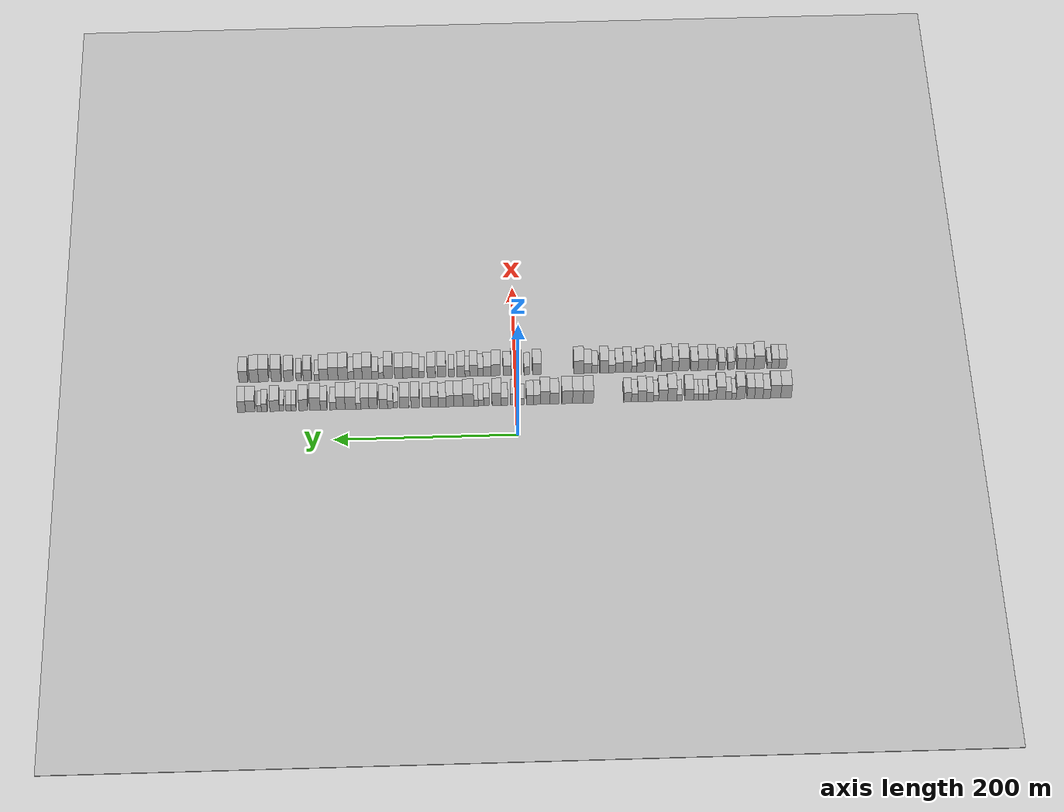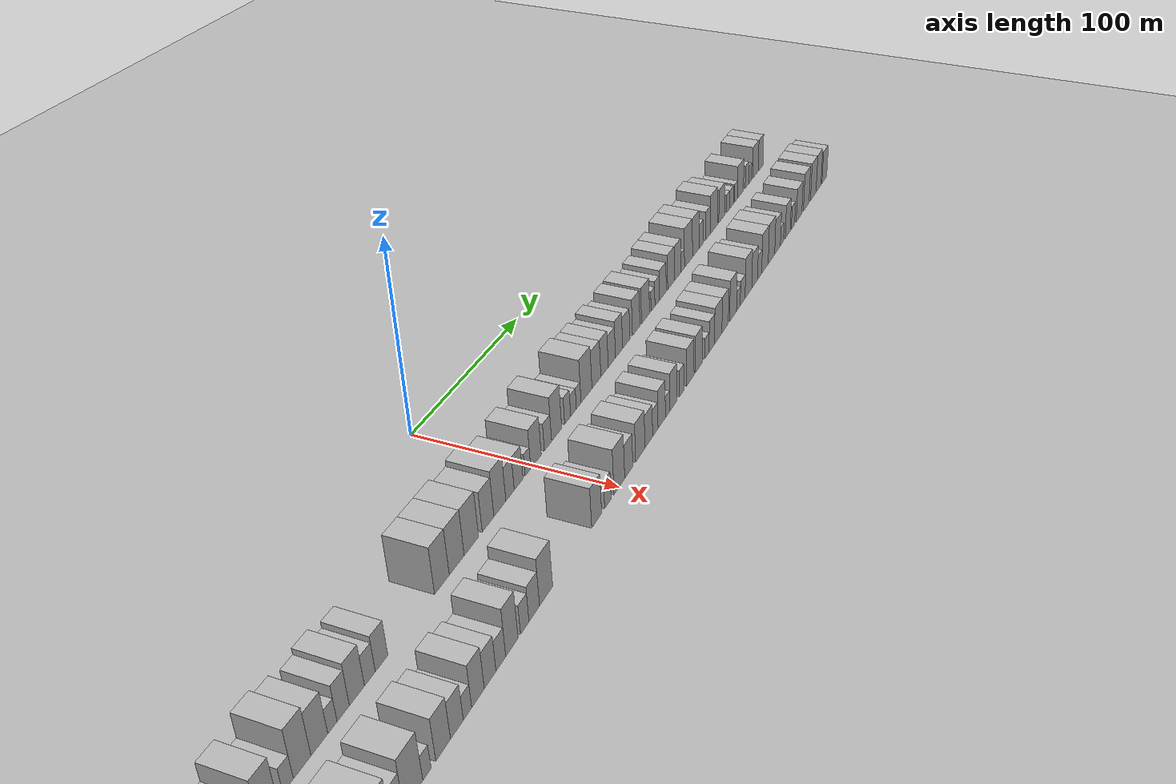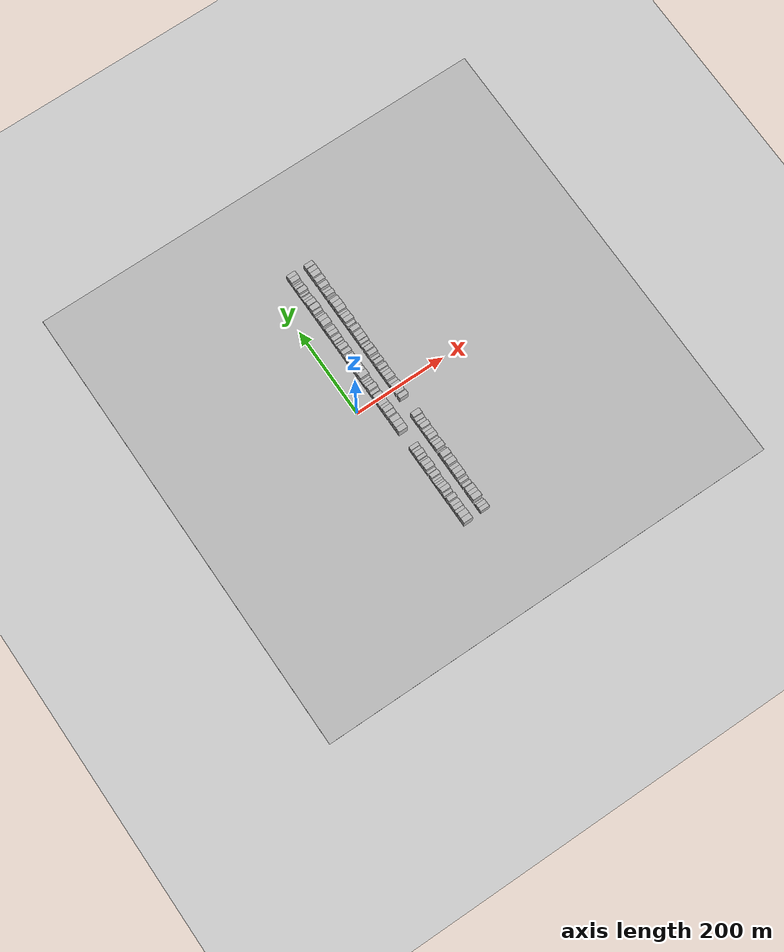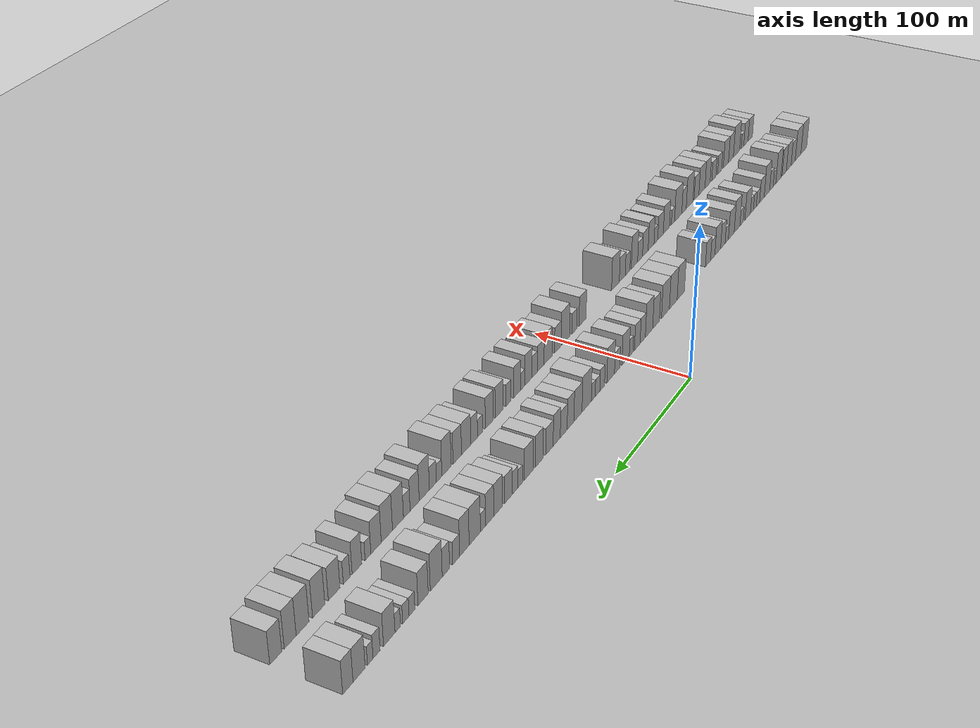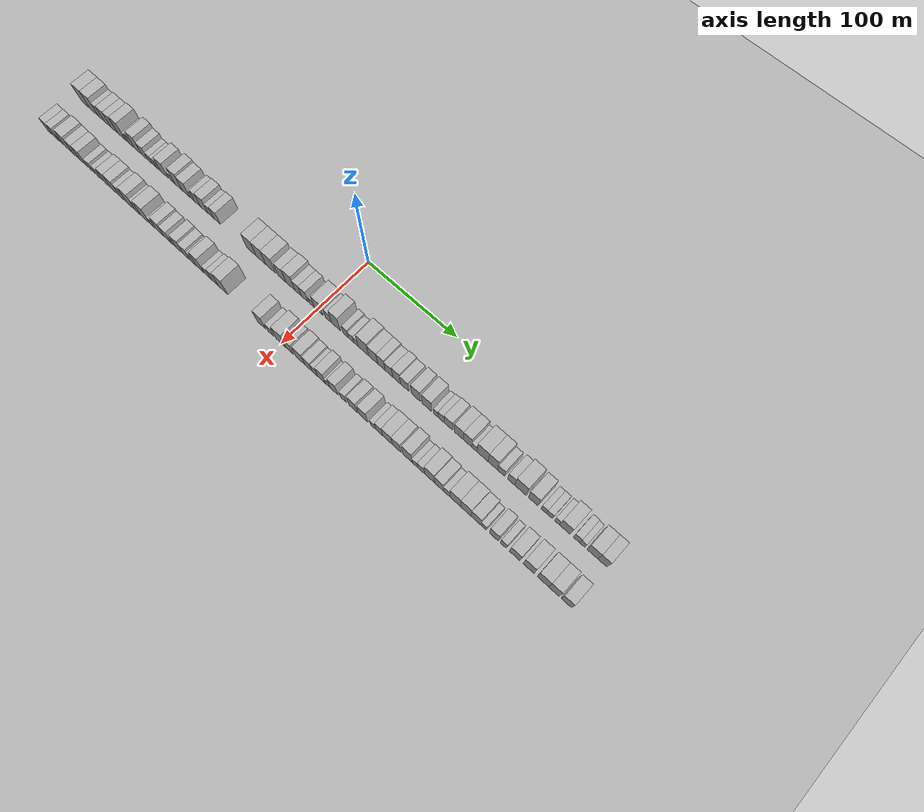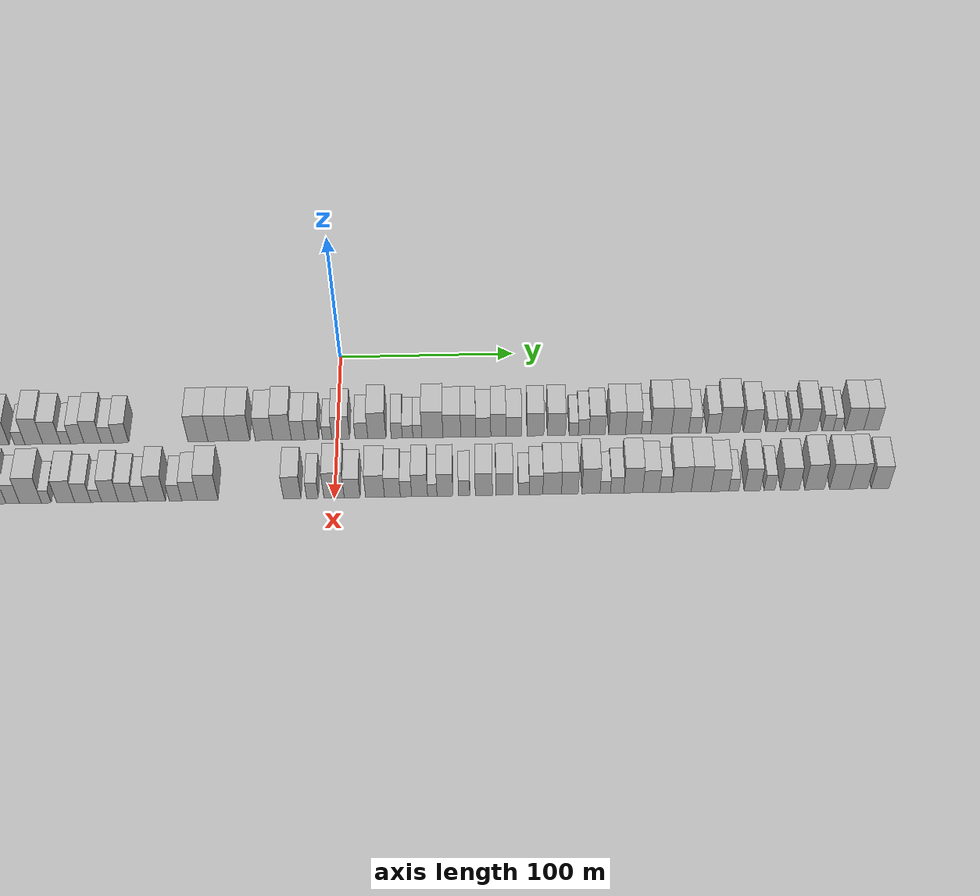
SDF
<?xml version="1.0" encoding="utf-8"?>

<sdf version="1.6">

   <world name="default">

      <gui fullscreen="0">

         <camera name="user_camera">

            <pose>-15 0 4.57585 0 0 0</pose>

            <view_controller>orbit</view_controller>

         </camera>

      </gui>

      <scene>

         <sky>

           <clouds>

             <speed>12</speed>

           </clouds>

         </sky>

         <ambient>0.4 0.4 0.4 1</ambient>

         <background>0.7 0.7 0.7 1</background>

         <shadows>1</shadows>

      </scene>

      <gravity>0 0 -9.8066</gravity>

      <magnetic_field>6e-06 2.3e-05 -4.2e-05</magnetic_field>

      <physics default="0" name="default_physics" type="ode">

         <ode>

            <solver>

               <type>quick</type>

               <iters>10</iters>

               <sor>1.0</sor>

               <use_dynamic_moi_rescaling>0</use_dynamic_moi_rescaling>

            </solver>

            <constraints>

               <cfm>0</cfm>

               <erp>0.2</erp>

               <contact_max_correcting_vel>100</contact_max_correcting_vel>

               <contact_surface_layer>0.001</contact_surface_layer>

            </constraints>

         </ode>

         <max_step_size>0.004</max_step_size>

         <real_time_factor>1</real_time_factor>

         <real_time_update_rate>250</real_time_update_rate>

      </physics>

      <light name="sun" type="directional">

         <cast_shadows>1</cast_shadows>

         <pose>0 0 10 0 0 0</pose>

         <diffuse>0.8 0.8 0.8 1</diffuse>

         <specular>0.2 0.2 0.2 1</specular>

         <attenuation>

            <range>1000</range>

            <constant>0.9</constant>

            <linear>0.01</linear>

            <quadratic>0.001</quadratic>

         </attenuation>

         <direction>-0.5 0.1 -0.9</direction>

      </light>

      <include>

         <name>ground_plane_1</name>

         <uri>model://HANNAS_ground_plane</uri>

         <pose>0 0 0  0 0 0</pose>

      </include>

      <include>

         <name>ground_plane_2</name>

         <uri>model://HANNAS_ground_plane</uri>

         <pose>100 0 0  0 0 0</pose>

      </include>

      <model name="building_1">

         <static>1</static>

         <pose frame="">50.0000 -294.1482 0 0.000000 0.000000 0.000000</pose>

         <link name="link">

            <pose frame="">0 0 12.00 0 0 0</pose>

            <collision name="collision">

               <geometry>

                  <box>

                     <size>20.0000 11.7035 24.0000</size>

                  </box>

               </geometry>

               <max_contacts>10</max_contacts>

               <surface>

                  <contact>

                     <ode/>

                  </contact>

                  <bounce/>

                  <friction>

                     <torsional>

                        <ode/>

                     </torsional>

                     <ode/>

                  </friction>

               </surface>

            </collision>

            <visual name="visual">

               <cast_shadows>0</cast_shadows>

               <geometry>

                  <box>

                     <size>20.0000 11.7035 24.0000</size>

                  </box>

               </geometry>

               <material>

                  <script>

                     <uri>model://HANNAS_wall/materials/scripts</uri>

                     <uri>model://HANNAS_wall/materials/textures</uri>

                     <name>vrc/HANNAS_wall</name>

                  </script>

               </material>

            </visual>

            <self_collide>0</self_collide>

            <enable_wind>0</enable_wind>

            <kinematic>0</kinematic>

         </link>

      </model>

      <model name="building_2">

         <static>1</static>

         <pose frame="">50.0000 -282.6605 0 0.000000 0.000000 0.000000</pose>

         <link name="link">

            <pose frame="">0 0 12.00 0 0 0</pose>

            <collision name="collision">

               <geometry>

                  <box>

                     <size>20.0000 11.2720 24.0000</size>

                  </box>

               </geometry>

               <max_contacts>10</max_contacts>

               <surface>

                  <contact>

                     <ode/>

                  </contact>

                  <bounce/>

                  <friction>

                     <torsional>

                        <ode/>

                     </torsional>

                     <ode/>

                  </friction>

               </surface>

            </collision>

            <visual name="visual">

               <cast_shadows>0</cast_shadows>

               <geometry>

                  <box>

                     <size>20.0000 11.2720 24.0000</size>

                  </box>

               </geometry>

               <material>

                  <script>

                     <uri>model://HANNAS_wall/materials/scripts</uri>

                     <uri>model://HANNAS_wall/materials/textures</uri>

                     <name>vrc/HANNAS_wall</name>

                  </script>

               </material>

            </visual>

            <self_collide>0</self_collide>

            <enable_wind>0</enable_wind>

            <kinematic>0</kinematic>

         </link>

      </model>

      <model name="building_3">

         <static>1</static>

         <pose frame="">50.0000 -272.9549 0 0.000000 0.000000 0.000000</pose>

         <link name="link">

            <pose frame="">0 0 9.00 0 0 0</pose>

            <collision name="collision">

               <geometry>

                  <box>

                     <size>20.0000 8.1390 18.0000</size>

                  </box>

               </geometry>

               <max_contacts>10</max_contacts>

               <surface>

                  <contact>

                     <ode/>

                  </contact>

                  <bounce/>

                  <friction>

                     <torsional>

                        <ode/>

                     </torsional>

                     <ode/>

                  </friction>

               </surface>

            </collision>

            <visual name="visual">

               <cast_shadows>0</cast_shadows>

               <geometry>

                  <box>

                     <size>20.0000 8.1390 18.0000</size>

                  </box>

               </geometry>

               <material>

                  <script>

                     <uri>model://HANNAS_wall/materials/scripts</uri>

                     <uri>model://HANNAS_wall/materials/textures</uri>

                     <name>vrc/HANNAS_wall</name>

                  </script>

               </material>

            </visual>

            <self_collide>0</self_collide>

            <enable_wind>0</enable_wind>

            <kinematic>0</kinematic>

         </link>

      </model>

      <model name="building_4">

         <static>1</static>

         <pose frame="">50.0000 -264.2775 0 0.000000 0.000000 0.000000</pose>

         <link name="link">

            <pose frame="">0 0 10.50 0 0 0</pose>

            <collision name="collision">

               <geometry>

                  <box>

                     <size>20.0000 9.2159 21.0000</size>

                  </box>

               </geometry>

               <max_contacts>10</max_contacts>

               <surface>

                  <contact>

                     <ode/>

                  </contact>

                  <bounce/>

                  <friction>

                     <torsional>

                        <ode/>

                     </torsional>

                     <ode/>

                  </friction>

               </surface>

            </collision>

            <visual name="visual">

               <cast_shadows>0</cast_shadows>

               <geometry>

                  <box>

                     <size>20.0000 9.2159 21.0000</size>

                  </box>

               </geometry>

               <material>

                  <script>

                     <uri>model://HANNAS_wall/materials/scripts</uri>

                     <uri>model://HANNAS_wall/materials/textures</uri>

                     <name>vrc/HANNAS_wall</name>

                  </script>

               </material>

            </visual>

            <self_collide>0</self_collide>

            <enable_wind>0</enable_wind>

            <kinematic>0</kinematic>

         </link>

      </model>

      <model name="building_5">

         <static>1</static>

         <pose frame="">50.0000 -255.4613 0 0.000000 0.000000 0.000000</pose>

         <link name="link">

            <pose frame="">0 0 10.50 0 0 0</pose>

            <collision name="collision">

               <geometry>

                  <box>

                     <size>20.0000 8.4165 21.0000</size>

                  </box>

               </geometry>

               <max_contacts>10</max_contacts>

               <surface>

                  <contact>

                     <ode/>

                  </contact>

                  <bounce/>

                  <friction>

                     <torsional>

                        <ode/>

                     </torsional>

                     <ode/>

                  </friction>

               </surface>

            </collision>

            <visual name="visual">

               <cast_shadows>0</cast_shadows>

               <geometry>

                  <box>

                     <size>20.0000 8.4165 21.0000</size>

                  </box>

               </geometry>

               <material>

                  <script>

                     <uri>model://HANNAS_wall/materials/scripts</uri>

                     <uri>model://HANNAS_wall/materials/textures</uri>

                     <name>vrc/HANNAS_wall</name>

                  </script>

               </material>

            </visual>

            <self_collide>0</self_collide>

            <enable_wind>0</enable_wind>

            <kinematic>0</kinematic>

         </link>

      </model>

      <model name="building_6">

         <static>1</static>

         <pose frame="">50.0000 -244.3734 0 0.000000 0.000000 0.000000</pose>

         <link name="link">

            <pose frame="">0 0 12.00 0 0 0</pose>

            <collision name="collision">

               <geometry>

                  <box>

                     <size>20.0000 9.7594 24.0000</size>

                  </box>

               </geometry>

               <max_contacts>10</max_contacts>

               <surface>

                  <contact>

                     <ode/>

                  </contact>

                  <bounce/>

                  <friction>

                     <torsional>

                        <ode/>

                     </torsional>

                     <ode/>

                  </friction>

               </surface>

            </collision>

            <visual name="visual">

               <cast_shadows>0</cast_shadows>

               <geometry>

                  <box>

                     <size>20.0000 9.7594 24.0000</size>

                  </box>

               </geometry>

               <material>

                  <script>

                     <uri>model://HANNAS_wall/materials/scripts</uri>

                     <uri>model://HANNAS_wall/materials/textures</uri>

                     <name>vrc/HANNAS_wall</name>

                  </script>

               </material>

            </visual>

            <self_collide>0</self_collide>

            <enable_wind>0</enable_wind>

            <kinematic>0</kinematic>

         </link>

      </model>

      <model name="building_7">

         <static>1</static>

         <pose frame="">50.0000 -237.0098 0 0.000000 0.000000 0.000000</pose>

         <link name="link">

            <pose frame="">0 0 6.00 0 0 0</pose>

            <collision name="collision">

               <geometry>

                  <box>

                     <size>20.0000 4.9678 12.0000</size>

                  </box>

               </geometry>

               <max_contacts>10</max_contacts>

               <surface>

                  <contact>

                     <ode/>

                  </contact>

                  <bounce/>

                  <friction>

                     <torsional>

                        <ode/>

                     </torsional>

                     <ode/>

                  </friction>

               </surface>

            </collision>

            <visual name="visual">

               <cast_shadows>0</cast_shadows>

               <geometry>

                  <box>

                     <size>20.0000 4.9678 12.0000</size>

                  </box>

               </geometry>

               <material>

                  <script>

                     <uri>model://HANNAS_wall/materials/scripts</uri>

                     <uri>model://HANNAS_wall/materials/textures</uri>

                     <name>vrc/HANNAS_wall</name>

                  </script>

               </material>

            </visual>

            <self_collide>0</self_collide>

            <enable_wind>0</enable_wind>

            <kinematic>0</kinematic>

         </link>

      </model>

      <model name="building_8">

         <static>1</static>

         <pose frame="">50.0000 -231.1403 0 0.000000 0.000000 0.000000</pose>

         <link name="link">

            <pose frame="">0 0 7.50 0 0 0</pose>

            <collision name="collision">

               <geometry>

                  <box>

                     <size>20.0000 6.7712 15.0000</size>

                  </box>

               </geometry>

               <max_contacts>10</max_contacts>

               <surface>

                  <contact>

                     <ode/>

                  </contact>

                  <bounce/>

                  <friction>

                     <torsional>

                        <ode/>

                     </torsional>

                     <ode/>

                  </friction>

               </surface>

            </collision>

            <visual name="visual">

               <cast_shadows>0</cast_shadows>

               <geometry>

                  <box>

                     <size>20.0000 6.7712 15.0000</size>

                  </box>

               </geometry>

               <material>

                  <script>

                     <uri>model://HANNAS_wall/materials/scripts</uri>

                     <uri>model://HANNAS_wall/materials/textures</uri>

                     <name>vrc/HANNAS_wall</name>

                  </script>

               </material>

            </visual>

            <self_collide>0</self_collide>

            <enable_wind>0</enable_wind>

            <kinematic>0</kinematic>

         </link>

      </model>

      <model name="building_9">

         <static>1</static>

         <pose frame="">50.0000 -222.8036 0 0.000000 0.000000 0.000000</pose>

         <link name="link">

            <pose frame="">0 0 12.00 0 0 0</pose>

            <collision name="collision">

               <geometry>

                  <box>

                     <size>20.0000 9.9022 24.0000</size>

                  </box>

               </geometry>

               <max_contacts>10</max_contacts>

               <surface>

                  <contact>

                     <ode/>

                  </contact>

                  <bounce/>

                  <friction>

                     <torsional>

                        <ode/>

                     </torsional>

                     <ode/>

                  </friction>

               </surface>

            </collision>

            <visual name="visual">

               <cast_shadows>0</cast_shadows>

               <geometry>

                  <box>

                     <size>20.0000 9.9022 24.0000</size>

                  </box>

               </geometry>

               <material>

                  <script>

                     <uri>model://HANNAS_wall/materials/scripts</uri>

                     <uri>model://HANNAS_wall/materials/textures</uri>

                     <name>vrc/HANNAS_wall</name>

                  </script>

               </material>

            </visual>

            <self_collide>0</self_collide>

            <enable_wind>0</enable_wind>

            <kinematic>0</kinematic>

         </link>

      </model>

      <model name="building_10">

         <static>1</static>

         <pose frame="">50.0000 -213.5388 0 0.000000 0.000000 0.000000</pose>

         <link name="link">

            <pose frame="">0 0 9.00 0 0 0</pose>

            <collision name="collision">

               <geometry>

                  <box>

                     <size>20.0000 8.6273 18.0000</size>

                  </box>

               </geometry>

               <max_contacts>10</max_contacts>

               <surface>

                  <contact>

                     <ode/>

                  </contact>

                  <bounce/>

                  <friction>

                     <torsional>

                        <ode/>

                     </torsional>

                     <ode/>

                  </friction>

               </surface>

            </collision>

            <visual name="visual">

               <cast_shadows>0</cast_shadows>

               <geometry>

                  <box>

                     <size>20.0000 8.6273 18.0000</size>

                  </box>

               </geometry>

               <material>

                  <script>

                     <uri>model://HANNAS_wall/materials/scripts</uri>

                     <uri>model://HANNAS_wall/materials/textures</uri>

                     <name>vrc/HANNAS_wall</name>

                  </script>

               </material>

            </visual>

            <self_collide>0</self_collide>

            <enable_wind>0</enable_wind>

            <kinematic>0</kinematic>

         </link>

      </model>

      <model name="building_11">

         <static>1</static>

         <pose frame="">50.0000 -206.2895 0 0.000000 0.000000 0.000000</pose>

         <link name="link">

            <pose frame="">0 0 6.00 0 0 0</pose>

            <collision name="collision">

               <geometry>

                  <box>

                     <size>20.0000 5.8713 12.0000</size>

                  </box>

               </geometry>

               <max_contacts>10</max_contacts>

               <surface>

                  <contact>

                     <ode/>

                  </contact>

                  <bounce/>

                  <friction>

                     <torsional>

                        <ode/>

                     </torsional>

                     <ode/>

                  </friction>

               </surface>

            </collision>

            <visual name="visual">

               <cast_shadows>0</cast_shadows>

               <geometry>

                  <box>

                     <size>20.0000 5.8713 12.0000</size>

                  </box>

               </geometry>

               <material>

                  <script>

                     <uri>model://HANNAS_wall/materials/scripts</uri>

                     <uri>model://HANNAS_wall/materials/textures</uri>

                     <name>vrc/HANNAS_wall</name>

                  </script>

               </material>

            </visual>

            <self_collide>0</self_collide>

            <enable_wind>0</enable_wind>

            <kinematic>0</kinematic>

         </link>

      </model>

      <model name="building_12">

         <static>1</static>

         <pose frame="">50.0000 -200.8021 0 0.000000 0.000000 0.000000</pose>

         <link name="link">

            <pose frame="">0 0 6.00 0 0 0</pose>

            <collision name="collision">

               <geometry>

                  <box>

                     <size>20.0000 5.1035 12.0000</size>

                  </box>

               </geometry>

               <max_contacts>10</max_contacts>

               <surface>

                  <contact>

                     <ode/>

                  </contact>

                  <bounce/>

                  <friction>

                     <torsional>

                        <ode/>

                     </torsional>

                     <ode/>

                  </friction>

               </surface>

            </collision>

            <visual name="visual">

               <cast_shadows>0</cast_shadows>

               <geometry>

                  <box>

                     <size>20.0000 5.1035 12.0000</size>

                  </box>

               </geometry>

               <material>

                  <script>

                     <uri>model://HANNAS_wall/materials/scripts</uri>

                     <uri>model://HANNAS_wall/materials/textures</uri>

                     <name>vrc/HANNAS_wall</name>

                  </script>

               </material>

            </visual>

            <self_collide>0</self_collide>

            <enable_wind>0</enable_wind>

            <kinematic>0</kinematic>

         </link>

      </model>

      <model name="building_13">

         <static>1</static>

         <pose frame="">50.0000 -195.5627 0 0.000000 0.000000 0.000000</pose>

         <link name="link">

            <pose frame="">0 0 6.00 0 0 0</pose>

            <collision name="collision">

               <geometry>

                  <box>

                     <size>20.0000 5.3754 12.0000</size>

                  </box>

               </geometry>

               <max_contacts>10</max_contacts>

               <surface>

                  <contact>

                     <ode/>

                  </contact>

                  <bounce/>

                  <friction>

                     <torsional>

                        <ode/>

                     </torsional>

                     <ode/>

                  </friction>

               </surface>

            </collision>

            <visual name="visual">

               <cast_shadows>0</cast_shadows>

               <geometry>

                  <box>

                     <size>20.0000 5.3754 12.0000</size>

                  </box>

               </geometry>

               <material>

                  <script>

                     <uri>model://HANNAS_wall/materials/scripts</uri>

                     <uri>model://HANNAS_wall/materials/textures</uri>

                     <name>vrc/HANNAS_wall</name>

                  </script>

               </material>

            </visual>

            <self_collide>0</self_collide>

            <enable_wind>0</enable_wind>

            <kinematic>0</kinematic>

         </link>

      </model>

      <model name="building_14">

         <static>1</static>

         <pose frame="">50.0000 -188.0589 0 0.000000 0.000000 0.000000</pose>

         <link name="link">

            <pose frame="">0 0 10.50 0 0 0</pose>

            <collision name="collision">

               <geometry>

                  <box>

                     <size>20.0000 9.6321 21.0000</size>

                  </box>

               </geometry>

               <max_contacts>10</max_contacts>

               <surface>

                  <contact>

                     <ode/>

                  </contact>

                  <bounce/>

                  <friction>

                     <torsional>

                        <ode/>

                     </torsional>

                     <ode/>

                  </friction>

               </surface>

            </collision>

            <visual name="visual">

               <cast_shadows>0</cast_shadows>

               <geometry>

                  <box>

                     <size>20.0000 9.6321 21.0000</size>

                  </box>

               </geometry>

               <material>

                  <script>

                     <uri>model://HANNAS_wall/materials/scripts</uri>

                     <uri>model://HANNAS_wall/materials/textures</uri>

                     <name>vrc/HANNAS_wall</name>

                  </script>

               </material>

            </visual>

            <self_collide>0</self_collide>

            <enable_wind>0</enable_wind>

            <kinematic>0</kinematic>

         </link>

      </model>

      <model name="building_15">

         <static>1</static>

         <pose frame="">50.0000 -177.3027 0 0.000000 0.000000 0.000000</pose>

         <link name="link">

            <pose frame="">0 0 6.00 0 0 0</pose>

            <collision name="collision">

               <geometry>

                  <box>

                     <size>20.0000 5.8805 12.0000</size>

                  </box>

               </geometry>

               <max_contacts>10</max_contacts>

               <surface>

                  <contact>

                     <ode/>

                  </contact>

                  <bounce/>

                  <friction>

                     <torsional>

                        <ode/>

                     </torsional>

                     <ode/>

                  </friction>

               </surface>

            </collision>

            <visual name="visual">

               <cast_shadows>0</cast_shadows>

               <geometry>

                  <box>

                     <size>20.0000 5.8805 12.0000</size>

                  </box>

               </geometry>

               <material>

                  <script>

                     <uri>model://HANNAS_wall/materials/scripts</uri>

                     <uri>model://HANNAS_wall/materials/textures</uri>

                     <name>vrc/HANNAS_wall</name>

                  </script>

               </material>

            </visual>

            <self_collide>0</self_collide>

            <enable_wind>0</enable_wind>

            <kinematic>0</kinematic>

         </link>

      </model>

      <model name="building_16">

         <static>1</static>

         <pose frame="">50.0000 -169.3864 0 0.000000 0.000000 0.000000</pose>

         <link name="link">

            <pose frame="">0 0 12.00 0 0 0</pose>

            <collision name="collision">

               <geometry>

                  <box>

                     <size>20.0000 9.9520 24.0000</size>

                  </box>

               </geometry>

               <max_contacts>10</max_contacts>

               <surface>

                  <contact>

                     <ode/>

                  </contact>

                  <bounce/>

                  <friction>

                     <torsional>

                        <ode/>

                     </torsional>

                     <ode/>

                  </friction>

               </surface>

            </collision>

            <visual name="visual">

               <cast_shadows>0</cast_shadows>

               <geometry>

                  <box>

                     <size>20.0000 9.9520 24.0000</size>

                  </box>

               </geometry>

               <material>

                  <script>

                     <uri>model://HANNAS_wall/materials/scripts</uri>

                     <uri>model://HANNAS_wall/materials/textures</uri>

                     <name>vrc/HANNAS_wall</name>

                  </script>

               </material>

            </visual>

            <self_collide>0</self_collide>

            <enable_wind>0</enable_wind>

            <kinematic>0</kinematic>

         </link>

      </model>

      <model name="building_17">

         <static>1</static>

         <pose frame="">50.0000 -159.4956 0 0.000000 0.000000 0.000000</pose>

         <link name="link">

            <pose frame="">0 0 10.50 0 0 0</pose>

            <collision name="collision">

               <geometry>

                  <box>

                     <size>20.0000 9.8298 21.0000</size>

                  </box>

               </geometry>

               <max_contacts>10</max_contacts>

               <surface>

                  <contact>

                     <ode/>

                  </contact>

                  <bounce/>

                  <friction>

                     <torsional>

                        <ode/>

                     </torsional>

                     <ode/>

                  </friction>

               </surface>

            </collision>

            <visual name="visual">

               <cast_shadows>0</cast_shadows>

               <geometry>

                  <box>

                     <size>20.0000 9.8298 21.0000</size>

                  </box>

               </geometry>

               <material>

                  <script>

                     <uri>model://HANNAS_wall/materials/scripts</uri>

                     <uri>model://HANNAS_wall/materials/textures</uri>

                     <name>vrc/HANNAS_wall</name>

                  </script>

               </material>

            </visual>

            <self_collide>0</self_collide>

            <enable_wind>0</enable_wind>

            <kinematic>0</kinematic>

         </link>

      </model>

      <model name="building_18">

         <static>1</static>

         <pose frame="">50.0000 -151.7910 0 0.000000 0.000000 0.000000</pose>

         <link name="link">

            <pose frame="">0 0 6.00 0 0 0</pose>

            <collision name="collision">

               <geometry>

                  <box>

                     <size>20.0000 5.5794 12.0000</size>

                  </box>

               </geometry>

               <max_contacts>10</max_contacts>

               <surface>

                  <contact>

                     <ode/>

                  </contact>

                  <bounce/>

                  <friction>

                     <torsional>

                        <ode/>

                     </torsional>

                     <ode/>

                  </friction>

               </surface>

            </collision>

            <visual name="visual">

               <cast_shadows>0</cast_shadows>

               <geometry>

                  <box>

                     <size>20.0000 5.5794 12.0000</size>

                  </box>

               </geometry>

               <material>

                  <script>

                     <uri>model://HANNAS_wall/materials/scripts</uri>

                     <uri>model://HANNAS_wall/materials/textures</uri>

                     <name>vrc/HANNAS_wall</name>

                  </script>

               </material>

            </visual>

            <self_collide>0</self_collide>

            <enable_wind>0</enable_wind>

            <kinematic>0</kinematic>

         </link>

      </model>

      <model name="building_19">

         <static>1</static>

         <pose frame="">50.0000 -145.2090 0 0.000000 0.000000 0.000000</pose>

         <link name="link">

            <pose frame="">0 0 9.00 0 0 0</pose>

            <collision name="collision">

               <geometry>

                  <box>

                     <size>20.0000 7.5845 18.0000</size>

                  </box>

               </geometry>

               <max_contacts>10</max_contacts>

               <surface>

                  <contact>

                     <ode/>

                  </contact>

                  <bounce/>

                  <friction>

                     <torsional>

                        <ode/>

                     </torsional>

                     <ode/>

                  </friction>

               </surface>

            </collision>

            <visual name="visual">

               <cast_shadows>0</cast_shadows>

               <geometry>

                  <box>

                     <size>20.0000 7.5845 18.0000</size>

                  </box>

               </geometry>

               <material>

                  <script>

                     <uri>model://HANNAS_wall/materials/scripts</uri>

                     <uri>model://HANNAS_wall/materials/textures</uri>

                     <name>vrc/HANNAS_wall</name>

                  </script>

               </material>

            </visual>

            <self_collide>0</self_collide>

            <enable_wind>0</enable_wind>

            <kinematic>0</kinematic>

         </link>

      </model>

      <model name="building_20">

         <static>1</static>

         <pose frame="">50.0000 -136.6767 0 0.000000 0.000000 0.000000</pose>

         <link name="link">

            <pose frame="">0 0 10.50 0 0 0</pose>

            <collision name="collision">

               <geometry>

                  <box>

                     <size>20.0000 9.4801 21.0000</size>

                  </box>

               </geometry>

               <max_contacts>10</max_contacts>

               <surface>

                  <contact>

                     <ode/>

                  </contact>

                  <bounce/>

                  <friction>

                     <torsional>

                        <ode/>

                     </torsional>

                     <ode/>

                  </friction>

               </surface>

            </collision>

            <visual name="visual">

               <cast_shadows>0</cast_shadows>

               <geometry>

                  <box>

                     <size>20.0000 9.4801 21.0000</size>

                  </box>

               </geometry>

               <material>

                  <script>

                     <uri>model://HANNAS_wall/materials/scripts</uri>

                     <uri>model://HANNAS_wall/materials/textures</uri>

                     <name>vrc/HANNAS_wall</name>

                  </script>

               </material>

            </visual>

            <self_collide>0</self_collide>

            <enable_wind>0</enable_wind>

            <kinematic>0</kinematic>

         </link>

      </model>

      <model name="building_21">

         <static>1</static>

         <pose frame="">50.0000 -128.4001 0 0.000000 0.000000 0.000000</pose>

         <link name="link">

            <pose frame="">0 0 7.50 0 0 0</pose>

            <collision name="collision">

               <geometry>

                  <box>

                     <size>20.0000 7.0731 15.0000</size>

                  </box>

               </geometry>

               <max_contacts>10</max_contacts>

               <surface>

                  <contact>

                     <ode/>

                  </contact>

                  <bounce/>

                  <friction>

                     <torsional>

                        <ode/>

                     </torsional>

                     <ode/>

                  </friction>

               </surface>

            </collision>

            <visual name="visual">

               <cast_shadows>0</cast_shadows>

               <geometry>

                  <box>

                     <size>20.0000 7.0731 15.0000</size>

                  </box>

               </geometry>

               <material>

                  <script>

                     <uri>model://HANNAS_wall/materials/scripts</uri>

                     <uri>model://HANNAS_wall/materials/textures</uri>

                     <name>vrc/HANNAS_wall</name>

                  </script>

               </material>

            </visual>

            <self_collide>0</self_collide>

            <enable_wind>0</enable_wind>

            <kinematic>0</kinematic>

         </link>

      </model>

      <model name="building_22">

         <static>1</static>

         <pose frame="">50.0000 -120.6991 0 0.000000 0.000000 0.000000</pose>

         <link name="link">

            <pose frame="">0 0 9.00 0 0 0</pose>

            <collision name="collision">

               <geometry>

                  <box>

                     <size>20.0000 8.3287 18.0000</size>

                  </box>

               </geometry>

               <max_contacts>10</max_contacts>

               <surface>

                  <contact>

                     <ode/>

                  </contact>

                  <bounce/>

                  <friction>

                     <torsional>

                        <ode/>

                     </torsional>

                     <ode/>

                  </friction>

               </surface>

            </collision>

            <visual name="visual">

               <cast_shadows>0</cast_shadows>

               <geometry>

                  <box>

                     <size>20.0000 8.3287 18.0000</size>

                  </box>

               </geometry>

               <material>

                  <script>

                     <uri>model://HANNAS_wall/materials/scripts</uri>

                     <uri>model://HANNAS_wall/materials/textures</uri>

                     <name>vrc/HANNAS_wall</name>

                  </script>

               </material>

            </visual>

            <self_collide>0</self_collide>

            <enable_wind>0</enable_wind>

            <kinematic>0</kinematic>

         </link>

      </model>

      <model name="building_23">

         <static>1</static>

         <pose frame="">50.0000 -77.7936 0 0.000000 0.000000 0.000000</pose>

         <link name="link">

            <pose frame="">0 0 12.00 0 0 0</pose>

            <collision name="collision">

               <geometry>

                  <box>

                     <size>20.0000 11.1608 24.0000</size>

                  </box>

               </geometry>

               <max_contacts>10</max_contacts>

               <surface>

                  <contact>

                     <ode/>

                  </contact>

                  <bounce/>

                  <friction>

                     <torsional>

                        <ode/>

                     </torsional>

                     <ode/>

                  </friction>

               </surface>

            </collision>

            <visual name="visual">

               <cast_shadows>0</cast_shadows>

               <geometry>

                  <box>

                     <size>20.0000 11.1608 24.0000</size>

                  </box>

               </geometry>

               <material>

                  <script>

                     <uri>model://HANNAS_wall/materials/scripts</uri>

                     <uri>model://HANNAS_wall/materials/textures</uri>

                     <name>vrc/HANNAS_wall</name>

                  </script>

               </material>

            </visual>

            <self_collide>0</self_collide>

            <enable_wind>0</enable_wind>

            <kinematic>0</kinematic>

         </link>

      </model>

      <model name="building_24">

         <static>1</static>

         <pose frame="">50.0000 -66.3565 0 0.000000 0.000000 0.000000</pose>

         <link name="link">

            <pose frame="">0 0 12.00 0 0 0</pose>

            <collision name="collision">

               <geometry>

                  <box>

                     <size>20.0000 11.7134 24.0000</size>

                  </box>

               </geometry>

               <max_contacts>10</max_contacts>

               <surface>

                  <contact>

                     <ode/>

                  </contact>

                  <bounce/>

                  <friction>

                     <torsional>

                        <ode/>

                     </torsional>

                     <ode/>

                  </friction>

               </surface>

            </collision>

            <visual name="visual">

               <cast_shadows>0</cast_shadows>

               <geometry>

                  <box>

                     <size>20.0000 11.7134 24.0000</size>

                  </box>

               </geometry>

               <material>

                  <script>

                     <uri>model://HANNAS_wall/materials/scripts</uri>

                     <uri>model://HANNAS_wall/materials/textures</uri>

                     <name>vrc/HANNAS_wall</name>

                  </script>

               </material>

            </visual>

            <self_collide>0</self_collide>

            <enable_wind>0</enable_wind>

            <kinematic>0</kinematic>

         </link>

      </model>

      <model name="building_25">

         <static>1</static>

         <pose frame="">50.0000 -54.6394 0 0.000000 0.000000 0.000000</pose>

         <link name="link">

            <pose frame="">0 0 12.00 0 0 0</pose>

            <collision name="collision">

               <geometry>

                  <box>

                     <size>20.0000 11.7207 24.0000</size>

                  </box>

               </geometry>

               <max_contacts>10</max_contacts>

               <surface>

                  <contact>

                     <ode/>

                  </contact>

                  <bounce/>

                  <friction>

                     <torsional>

                        <ode/>

                     </torsional>

                     <ode/>

                  </friction>

               </surface>

            </collision>

            <visual name="visual">

               <cast_shadows>0</cast_shadows>

               <geometry>

                  <box>

                     <size>20.0000 11.7207 24.0000</size>

                  </box>

               </geometry>

               <material>

                  <script>

                     <uri>model://HANNAS_wall/materials/scripts</uri>

                     <uri>model://HANNAS_wall/materials/textures</uri>

                     <name>vrc/HANNAS_wall</name>

                  </script>

               </material>

            </visual>

            <self_collide>0</self_collide>

            <enable_wind>0</enable_wind>

            <kinematic>0</kinematic>

         </link>

      </model>

      <model name="building_26">

         <static>1</static>

         <pose frame="">50.0000 -40.8496 0 0.000000 0.000000 0.000000</pose>

         <link name="link">

            <pose frame="">0 0 10.50 0 0 0</pose>

            <collision name="collision">

               <geometry>

                  <box>

                     <size>20.0000 9.8590 21.0000</size>

                  </box>

               </geometry>

               <max_contacts>10</max_contacts>

               <surface>

                  <contact>

                     <ode/>

                  </contact>

                  <bounce/>

                  <friction>

                     <torsional>

                        <ode/>

                     </torsional>

                     <ode/>

                  </friction>

               </surface>

            </collision>

            <visual name="visual">

               <cast_shadows>0</cast_shadows>

               <geometry>

                  <box>

                     <size>20.0000 9.8590 21.0000</size>

                  </box>

               </geometry>

               <material>

                  <script>

                     <uri>model://HANNAS_wall/materials/scripts</uri>

                     <uri>model://HANNAS_wall/materials/textures</uri>

                     <name>vrc/HANNAS_wall</name>

                  </script>

               </material>

            </visual>

            <self_collide>0</self_collide>

            <enable_wind>0</enable_wind>

            <kinematic>0</kinematic>

         </link>

      </model>

      <model name="building_27">

         <static>1</static>

         <pose frame="">50.0000 -30.7052 0 0.000000 0.000000 0.000000</pose>

         <link name="link">

            <pose frame="">0 0 12.00 0 0 0</pose>

            <collision name="collision">

               <geometry>

                  <box>

                     <size>20.0000 10.4298 24.0000</size>

                  </box>

               </geometry>

               <max_contacts>10</max_contacts>

               <surface>

                  <contact>

                     <ode/>

                  </contact>

                  <bounce/>

                  <friction>

                     <torsional>

                        <ode/>

                     </torsional>

                     <ode/>

                  </friction>

               </surface>

            </collision>

            <visual name="visual">

               <cast_shadows>0</cast_shadows>

               <geometry>

                  <box>

                     <size>20.0000 10.4298 24.0000</size>

                  </box>

               </geometry>

               <material>

                  <script>

                     <uri>model://HANNAS_wall/materials/scripts</uri>

                     <uri>model://HANNAS_wall/materials/textures</uri>

                     <name>vrc/HANNAS_wall</name>

                  </script>

               </material>

            </visual>

            <self_collide>0</self_collide>

            <enable_wind>0</enable_wind>

            <kinematic>0</kinematic>

         </link>

      </model>

      <model name="building_28">

         <static>1</static>

         <pose frame="">50.0000 -21.7638 0 0.000000 0.000000 0.000000</pose>

         <link name="link">

            <pose frame="">0 0 9.00 0 0 0</pose>

            <collision name="collision">

               <geometry>

                  <box>

                     <size>20.0000 7.4530 18.0000</size>

                  </box>

               </geometry>

               <max_contacts>10</max_contacts>

               <surface>

                  <contact>

                     <ode/>

                  </contact>

                  <bounce/>

                  <friction>

                     <torsional>

                        <ode/>

                     </torsional>

                     <ode/>

                  </friction>

               </surface>

            </collision>

            <visual name="visual">

               <cast_shadows>0</cast_shadows>

               <geometry>

                  <box>

                     <size>20.0000 7.4530 18.0000</size>

                  </box>

               </geometry>

               <material>

                  <script>

                     <uri>model://HANNAS_wall/materials/scripts</uri>

                     <uri>model://HANNAS_wall/materials/textures</uri>

                     <name>vrc/HANNAS_wall</name>

                  </script>

               </material>

            </visual>

            <self_collide>0</self_collide>

            <enable_wind>0</enable_wind>

            <kinematic>0</kinematic>

         </link>

      </model>

      <model name="building_29">

         <static>1</static>

         <pose frame="">50.0000 -14.0712 0 0.000000 0.000000 0.000000</pose>

         <link name="link">

            <pose frame="">0 0 9.00 0 0 0</pose>

            <collision name="collision">

               <geometry>

                  <box>

                     <size>20.0000 7.9321 18.0000</size>

                  </box>

               </geometry>

               <max_contacts>10</max_contacts>

               <surface>

                  <contact>

                     <ode/>

                  </contact>

                  <bounce/>

                  <friction>

                     <torsional>

                        <ode/>

                     </torsional>

                     <ode/>

                  </friction>

               </surface>

            </collision>

            <visual name="visual">

               <cast_shadows>0</cast_shadows>

               <geometry>

                  <box>

                     <size>20.0000 7.9321 18.0000</size>

                  </box>

               </geometry>

               <material>

                  <script>

                     <uri>model://HANNAS_wall/materials/scripts</uri>

                     <uri>model://HANNAS_wall/materials/textures</uri>

                     <name>vrc/HANNAS_wall</name>

                  </script>

               </material>

            </visual>

            <self_collide>0</self_collide>

            <enable_wind>0</enable_wind>

            <kinematic>0</kinematic>

         </link>

      </model>

      <model name="building_30">

         <static>1</static>

         <pose frame="">50.0000 -5.4879 0 0.000000 0.000000 0.000000</pose>

         <link name="link">

            <pose frame="">0 0 6.00 0 0 0</pose>

            <collision name="collision">

               <geometry>

                  <box>

                     <size>20.0000 5.2346 12.0000</size>

                  </box>

               </geometry>

               <max_contacts>10</max_contacts>

               <surface>

                  <contact>

                     <ode/>

                  </contact>

                  <bounce/>

                  <friction>

                     <torsional>

                        <ode/>

                     </torsional>

                     <ode/>

                  </friction>

               </surface>

            </collision>

            <visual name="visual">

               <cast_shadows>0</cast_shadows>

               <geometry>

                  <box>

                     <size>20.0000 5.2346 12.0000</size>

                  </box>

               </geometry>

               <material>

                  <script>

                     <uri>model://HANNAS_wall/materials/scripts</uri>

                     <uri>model://HANNAS_wall/materials/textures</uri>

                     <name>vrc/HANNAS_wall</name>

                  </script>

               </material>

            </visual>

            <self_collide>0</self_collide>

            <enable_wind>0</enable_wind>

            <kinematic>0</kinematic>

         </link>

      </model>

      <model name="building_31">

         <static>1</static>

         <pose frame="">50.0000 2.1301 0 0.000000 0.000000 0.000000</pose>

         <link name="link">

            <pose frame="">0 0 10.50 0 0 0</pose>

            <collision name="collision">

               <geometry>

                  <box>

                     <size>20.0000 10.0014 21.0000</size>

                  </box>

               </geometry>

               <max_contacts>10</max_contacts>

               <surface>

                  <contact>

                     <ode/>

                  </contact>

                  <bounce/>

                  <friction>

                     <torsional>

                        <ode/>

                     </torsional>

                     <ode/>

                  </friction>

               </surface>

            </collision>

            <visual name="visual">

               <cast_shadows>0</cast_shadows>

               <geometry>

                  <box>

                     <size>20.0000 10.0014 21.0000</size>

                  </box>

               </geometry>

               <material>

                  <script>

                     <uri>model://HANNAS_wall/materials/scripts</uri>

                     <uri>model://HANNAS_wall/materials/textures</uri>

                     <name>vrc/HANNAS_wall</name>

                  </script>

               </material>

            </visual>

            <self_collide>0</self_collide>

            <enable_wind>0</enable_wind>

            <kinematic>0</kinematic>

         </link>

      </model>

      <model name="building_32">

         <static>1</static>

         <pose frame="">50.0000 13.6980 0 0.000000 0.000000 0.000000</pose>

         <link name="link">

            <pose frame="">0 0 7.50 0 0 0</pose>

            <collision name="collision">

               <geometry>

                  <box>

                     <size>20.0000 7.1344 15.0000</size>

                  </box>

               </geometry>

               <max_contacts>10</max_contacts>

               <surface>

                  <contact>

                     <ode/>

                  </contact>

                  <bounce/>

                  <friction>

                     <torsional>

                        <ode/>

                     </torsional>

                     <ode/>

                  </friction>

               </surface>

            </collision>

            <visual name="visual">

               <cast_shadows>0</cast_shadows>

               <geometry>

                  <box>

                     <size>20.0000 7.1344 15.0000</size>

                  </box>

               </geometry>

               <material>

                  <script>

                     <uri>model://HANNAS_wall/materials/scripts</uri>

                     <uri>model://HANNAS_wall/materials/textures</uri>

                     <name>vrc/HANNAS_wall</name>

                  </script>

               </material>

            </visual>

            <self_collide>0</self_collide>

            <enable_wind>0</enable_wind>

            <kinematic>0</kinematic>

         </link>

      </model>

      <model name="building_33">

         <static>1</static>

         <pose frame="">50.0000 22.3238 0 0.000000 0.000000 0.000000</pose>

         <link name="link">

            <pose frame="">0 0 12.00 0 0 0</pose>

            <collision name="collision">

               <geometry>

                  <box>

                     <size>20.0000 10.1171 24.0000</size>

                  </box>

               </geometry>

               <max_contacts>10</max_contacts>

               <surface>

                  <contact>

                     <ode/>

                  </contact>

                  <bounce/>

                  <friction>

                     <torsional>

                        <ode/>

                     </torsional>

                     <ode/>

                  </friction>

               </surface>

            </collision>

            <visual name="visual">

               <cast_shadows>0</cast_shadows>

               <geometry>

                  <box>

                     <size>20.0000 10.1171 24.0000</size>

                  </box>

               </geometry>

               <material>

                  <script>

                     <uri>model://HANNAS_wall/materials/scripts</uri>

                     <uri>model://HANNAS_wall/materials/textures</uri>

                     <name>vrc/HANNAS_wall</name>

                  </script>

               </material>

            </visual>

            <self_collide>0</self_collide>

            <enable_wind>0</enable_wind>

            <kinematic>0</kinematic>

         </link>

      </model>

      <model name="building_34">

         <static>1</static>

         <pose frame="">50.0000 33.4924 0 0.000000 0.000000 0.000000</pose>

         <link name="link">

            <pose frame="">0 0 7.50 0 0 0</pose>

            <collision name="collision">

               <geometry>

                  <box>

                     <size>20.0000 6.2201 15.0000</size>

                  </box>

               </geometry>

               <max_contacts>10</max_contacts>

               <surface>

                  <contact>

                     <ode/>

                  </contact>

                  <bounce/>

                  <friction>

                     <torsional>

                        <ode/>

                     </torsional>

                     <ode/>

                  </friction>

               </surface>

            </collision>

            <visual name="visual">

               <cast_shadows>0</cast_shadows>

               <geometry>

                  <box>

                     <size>20.0000 6.2201 15.0000</size>

                  </box>

               </geometry>

               <material>

                  <script>

                     <uri>model://HANNAS_wall/materials/scripts</uri>

                     <uri>model://HANNAS_wall/materials/textures</uri>

                     <name>vrc/HANNAS_wall</name>

                  </script>

               </material>

            </visual>

            <self_collide>0</self_collide>

            <enable_wind>0</enable_wind>

            <kinematic>0</kinematic>

         </link>

      </model>

      <model name="building_35">

         <static>1</static>

         <pose frame="">50.0000 39.5580 0 0.000000 0.000000 0.000000</pose>

         <link name="link">

            <pose frame="">0 0 6.00 0 0 0</pose>

            <collision name="collision">

               <geometry>

                  <box>

                     <size>20.0000 5.9111 12.0000</size>

                  </box>

               </geometry>

               <max_contacts>10</max_contacts>

               <surface>

                  <contact>

                     <ode/>

                  </contact>

                  <bounce/>

                  <friction>

                     <torsional>

                        <ode/>

                     </torsional>

                     <ode/>

                  </friction>

               </surface>

            </collision>

            <visual name="visual">

               <cast_shadows>0</cast_shadows>

               <geometry>

                  <box>

                     <size>20.0000 5.9111 12.0000</size>

                  </box>

               </geometry>

               <material>

                  <script>

                     <uri>model://HANNAS_wall/materials/scripts</uri>

                     <uri>model://HANNAS_wall/materials/textures</uri>

                     <name>vrc/HANNAS_wall</name>

                  </script>

               </material>

            </visual>

            <self_collide>0</self_collide>

            <enable_wind>0</enable_wind>

            <kinematic>0</kinematic>

         </link>

      </model>

      <model name="building_36">

         <static>1</static>

         <pose frame="">50.0000 45.0231 0 0.000000 0.000000 0.000000</pose>

         <link name="link">

            <pose frame="">0 0 6.00 0 0 0</pose>

            <collision name="collision">

               <geometry>

                  <box>

                     <size>20.0000 5.0190 12.0000</size>

                  </box>

               </geometry>

               <max_contacts>10</max_contacts>

               <surface>

                  <contact>

                     <ode/>

                  </contact>

                  <bounce/>

                  <friction>

                     <torsional>

                        <ode/>

                     </torsional>

                     <ode/>

                  </friction>

               </surface>

            </collision>

            <visual name="visual">

               <cast_shadows>0</cast_shadows>

               <geometry>

                  <box>

                     <size>20.0000 5.0190 12.0000</size>

                  </box>

               </geometry>

               <material>

                  <script>

                     <uri>model://HANNAS_wall/materials/scripts</uri>

                     <uri>model://HANNAS_wall/materials/textures</uri>

                     <name>vrc/HANNAS_wall</name>

                  </script>

               </material>

            </visual>

            <self_collide>0</self_collide>

            <enable_wind>0</enable_wind>

            <kinematic>0</kinematic>

         </link>

      </model>

      <model name="building_37">

         <static>1</static>

         <pose frame="">50.0000 53.4516 0 0.000000 0.000000 0.000000</pose>

         <link name="link">

            <pose frame="">0 0 12.00 0 0 0</pose>

            <collision name="collision">

               <geometry>

                  <box>

                     <size>20.0000 11.8379 24.0000</size>

                  </box>

               </geometry>

               <max_contacts>10</max_contacts>

               <surface>

                  <contact>

                     <ode/>

                  </contact>

                  <bounce/>

                  <friction>

                     <torsional>

                        <ode/>

                     </torsional>

                     <ode/>

                  </friction>

               </surface>

            </collision>

            <visual name="visual">

               <cast_shadows>0</cast_shadows>

               <geometry>

                  <box>

                     <size>20.0000 11.8379 24.0000</size>

                  </box>

               </geometry>

               <material>

                  <script>

                     <uri>model://HANNAS_wall/materials/scripts</uri>

                     <uri>model://HANNAS_wall/materials/textures</uri>

                     <name>vrc/HANNAS_wall</name>

                  </script>

               </material>

            </visual>

            <self_collide>0</self_collide>

            <enable_wind>0</enable_wind>

            <kinematic>0</kinematic>

         </link>

      </model>

      <model name="building_38">

         <static>1</static>

         <pose frame="">50.0000 64.3555 0 0.000000 0.000000 0.000000</pose>

         <link name="link">

            <pose frame="">0 0 10.50 0 0 0</pose>

            <collision name="collision">

               <geometry>

                  <box>

                     <size>20.0000 9.9698 21.0000</size>

                  </box>

               </geometry>

               <max_contacts>10</max_contacts>

               <surface>

                  <contact>

                     <ode/>

                  </contact>

                  <bounce/>

                  <friction>

                     <torsional>

                        <ode/>

                     </torsional>

                     <ode/>

                  </friction>

               </surface>

            </collision>

            <visual name="visual">

               <cast_shadows>0</cast_shadows>

               <geometry>

                  <box>

                     <size>20.0000 9.9698 21.0000</size>

                  </box>

               </geometry>

               <material>

                  <script>

                     <uri>model://HANNAS_wall/materials/scripts</uri>

                     <uri>model://HANNAS_wall/materials/textures</uri>

                     <name>vrc/HANNAS_wall</name>

                  </script>

               </material>

            </visual>

            <self_collide>0</self_collide>

            <enable_wind>0</enable_wind>

            <kinematic>0</kinematic>

         </link>

      </model>

      <model name="building_39">

         <static>1</static>

         <pose frame="">50.0000 73.5436 0 0.000000 0.000000 0.000000</pose>

         <link name="link">

            <pose frame="">0 0 10.50 0 0 0</pose>

            <collision name="collision">

               <geometry>

                  <box>

                     <size>20.0000 8.4065 21.0000</size>

                  </box>

               </geometry>

               <max_contacts>10</max_contacts>

               <surface>

                  <contact>

                     <ode/>

                  </contact>

                  <bounce/>

                  <friction>

                     <torsional>

                        <ode/>

                     </torsional>

                     <ode/>

                  </friction>

               </surface>

            </collision>

            <visual name="visual">

               <cast_shadows>0</cast_shadows>

               <geometry>

                  <box>

                     <size>20.0000 8.4065 21.0000</size>

                  </box>

               </geometry>

               <material>

                  <script>

                     <uri>model://HANNAS_wall/materials/scripts</uri>

                     <uri>model://HANNAS_wall/materials/textures</uri>

                     <name>vrc/HANNAS_wall</name>

                  </script>

               </material>

            </visual>

            <self_collide>0</self_collide>

            <enable_wind>0</enable_wind>

            <kinematic>0</kinematic>

         </link>

      </model>

      <model name="building_40">

         <static>1</static>

         <pose frame="">50.0000 81.9628 0 0.000000 0.000000 0.000000</pose>

         <link name="link">

            <pose frame="">0 0 9.00 0 0 0</pose>

            <collision name="collision">

               <geometry>

                  <box>

                     <size>20.0000 8.4319 18.0000</size>

                  </box>

               </geometry>

               <max_contacts>10</max_contacts>

               <surface>

                  <contact>

                     <ode/>

                  </contact>

                  <bounce/>

                  <friction>

                     <torsional>

                        <ode/>

                     </torsional>

                     <ode/>

                  </friction>

               </surface>

            </collision>

            <visual name="visual">

               <cast_shadows>0</cast_shadows>

               <geometry>

                  <box>

                     <size>20.0000 8.4319 18.0000</size>

                  </box>

               </geometry>

               <material>

                  <script>

                     <uri>model://HANNAS_wall/materials/scripts</uri>

                     <uri>model://HANNAS_wall/materials/textures</uri>

                     <name>vrc/HANNAS_wall</name>

                  </script>

               </material>

            </visual>

            <self_collide>0</self_collide>

            <enable_wind>0</enable_wind>

            <kinematic>0</kinematic>

         </link>

      </model>

      <model name="building_41">

         <static>1</static>

         <pose frame="">50.0000 90.4274 0 0.000000 0.000000 0.000000</pose>

         <link name="link">

            <pose frame="">0 0 10.50 0 0 0</pose>

            <collision name="collision">

               <geometry>

                  <box>

                     <size>20.0000 8.4972 21.0000</size>

                  </box>

               </geometry>

               <max_contacts>10</max_contacts>

               <surface>

                  <contact>

                     <ode/>

                  </contact>

                  <bounce/>

                  <friction>

                     <torsional>

                        <ode/>

                     </torsional>

                     <ode/>

                  </friction>

               </surface>

            </collision>

            <visual name="visual">

               <cast_shadows>0</cast_shadows>

               <geometry>

                  <box>

                     <size>20.0000 8.4972 21.0000</size>

                  </box>

               </geometry>

               <material>

                  <script>

                     <uri>model://HANNAS_wall/materials/scripts</uri>

                     <uri>model://HANNAS_wall/materials/textures</uri>

                     <name>vrc/HANNAS_wall</name>

                  </script>

               </material>

            </visual>

            <self_collide>0</self_collide>

            <enable_wind>0</enable_wind>

            <kinematic>0</kinematic>

         </link>

      </model>

      <model name="building_42">

         <static>1</static>

         <pose frame="">50.0000 99.1156 0 0.000000 0.000000 0.000000</pose>

         <link name="link">

            <pose frame="">0 0 9.00 0 0 0</pose>

            <collision name="collision">

               <geometry>

                  <box>

                     <size>20.0000 8.8792 18.0000</size>

                  </box>

               </geometry>

               <max_contacts>10</max_contacts>

               <surface>

                  <contact>

                     <ode/>

                  </contact>

                  <bounce/>

                  <friction>

                     <torsional>

                        <ode/>

                     </torsional>

                     <ode/>

                  </friction>

               </surface>

            </collision>

            <visual name="visual">

               <cast_shadows>0</cast_shadows>

               <geometry>

                  <box>

                     <size>20.0000 8.8792 18.0000</size>

                  </box>

               </geometry>

               <material>

                  <script>

                     <uri>model://HANNAS_wall/materials/scripts</uri>

                     <uri>model://HANNAS_wall/materials/textures</uri>

                     <name>vrc/HANNAS_wall</name>

                  </script>

               </material>

            </visual>

            <self_collide>0</self_collide>

            <enable_wind>0</enable_wind>

            <kinematic>0</kinematic>

         </link>

      </model>

      <model name="building_43">

         <static>1</static>

         <pose frame="">50.0000 111.2433 0 0.000000 0.000000 0.000000</pose>

         <link name="link">

            <pose frame="">0 0 10.50 0 0 0</pose>

            <collision name="collision">

               <geometry>

                  <box>

                     <size>20.0000 9.3763 21.0000</size>

                  </box>

               </geometry>

               <max_contacts>10</max_contacts>

               <surface>

                  <contact>

                     <ode/>

                  </contact>

                  <bounce/>

                  <friction>

                     <torsional>

                        <ode/>

                     </torsional>

                     <ode/>

                  </friction>

               </surface>

            </collision>

            <visual name="visual">

               <cast_shadows>0</cast_shadows>

               <geometry>

                  <box>

                     <size>20.0000 9.3763 21.0000</size>

                  </box>

               </geometry>

               <material>

                  <script>

                     <uri>model://HANNAS_wall/materials/scripts</uri>

                     <uri>model://HANNAS_wall/materials/textures</uri>

                     <name>vrc/HANNAS_wall</name>

                  </script>

               </material>

            </visual>

            <self_collide>0</self_collide>

            <enable_wind>0</enable_wind>

            <kinematic>0</kinematic>

         </link>

      </model>

      <model name="building_44">

         <static>1</static>

         <pose frame="">50.0000 123.0411 0 0.000000 0.000000 0.000000</pose>

         <link name="link">

            <pose frame="">0 0 10.50 0 0 0</pose>

            <collision name="collision">

               <geometry>

                  <box>

                     <size>20.0000 10.2192 21.0000</size>

                  </box>

               </geometry>

               <max_contacts>10</max_contacts>

               <surface>

                  <contact>

                     <ode/>

                  </contact>

                  <bounce/>

                  <friction>

                     <torsional>

                        <ode/>

                     </torsional>

                     <ode/>

                  </friction>

               </surface>

            </collision>

            <visual name="visual">

               <cast_shadows>0</cast_shadows>

               <geometry>

                  <box>

                     <size>20.0000 10.2192 21.0000</size>

                  </box>

               </geometry>

               <material>

                  <script>

                     <uri>model://HANNAS_wall/materials/scripts</uri>

                     <uri>model://HANNAS_wall/materials/textures</uri>

                     <name>vrc/HANNAS_wall</name>

                  </script>

               </material>

            </visual>

            <self_collide>0</self_collide>

            <enable_wind>0</enable_wind>

            <kinematic>0</kinematic>

         </link>

      </model>

      <model name="building_45">

         <static>1</static>

         <pose frame="">50.0000 132.7010 0 0.000000 0.000000 0.000000</pose>

         <link name="link">

            <pose frame="">0 0 6.00 0 0 0</pose>

            <collision name="collision">

               <geometry>

                  <box>

                     <size>20.0000 5.1006 12.0000</size>

                  </box>

               </geometry>

               <max_contacts>10</max_contacts>

               <surface>

                  <contact>

                     <ode/>

                  </contact>

                  <bounce/>

                  <friction>

                     <torsional>

                        <ode/>

                     </torsional>

                     <ode/>

                  </friction>

               </surface>

            </collision>

            <visual name="visual">

               <cast_shadows>0</cast_shadows>

               <geometry>

                  <box>

                     <size>20.0000 5.1006 12.0000</size>

                  </box>

               </geometry>

               <material>

                  <script>

                     <uri>model://HANNAS_wall/materials/scripts</uri>

                     <uri>model://HANNAS_wall/materials/textures</uri>

                     <name>vrc/HANNAS_wall</name>

                  </script>

               </material>

            </visual>

            <self_collide>0</self_collide>

            <enable_wind>0</enable_wind>

            <kinematic>0</kinematic>

         </link>

      </model>

      <model name="building_46">

         <static>1</static>

         <pose frame="">50.0000 138.3369 0 0.000000 0.000000 0.000000</pose>

         <link name="link">

            <pose frame="">0 0 7.50 0 0 0</pose>

            <collision name="collision">

               <geometry>

                  <box>

                     <size>20.0000 6.1713 15.0000</size>

                  </box>

               </geometry>

               <max_contacts>10</max_contacts>

               <surface>

                  <contact>

                     <ode/>

                  </contact>

                  <bounce/>

                  <friction>

                     <torsional>

                        <ode/>

                     </torsional>

                     <ode/>

                  </friction>

               </surface>

            </collision>

            <visual name="visual">

               <cast_shadows>0</cast_shadows>

               <geometry>

                  <box>

                     <size>20.0000 6.1713 15.0000</size>

                  </box>

               </geometry>

               <material>

                  <script>

                     <uri>model://HANNAS_wall/materials/scripts</uri>

                     <uri>model://HANNAS_wall/materials/textures</uri>

                     <name>vrc/HANNAS_wall</name>

                  </script>

               </material>

            </visual>

            <self_collide>0</self_collide>

            <enable_wind>0</enable_wind>

            <kinematic>0</kinematic>

         </link>

      </model>

      <model name="building_47">

         <static>1</static>

         <pose frame="">50.0000 145.9093 0 0.000000 0.000000 0.000000</pose>

         <link name="link">

            <pose frame="">0 0 9.00 0 0 0</pose>

            <collision name="collision">

               <geometry>

                  <box>

                     <size>20.0000 8.9736 18.0000</size>

                  </box>

               </geometry>

               <max_contacts>10</max_contacts>

               <surface>

                  <contact>

                     <ode/>

                  </contact>

                  <bounce/>

                  <friction>

                     <torsional>

                        <ode/>

                     </torsional>

                     <ode/>

                  </friction>

               </surface>

            </collision>

            <visual name="visual">

               <cast_shadows>0</cast_shadows>

               <geometry>

                  <box>

                     <size>20.0000 8.9736 18.0000</size>

                  </box>

               </geometry>

               <material>

                  <script>

                     <uri>model://HANNAS_wall/materials/scripts</uri>

                     <uri>model://HANNAS_wall/materials/textures</uri>

                     <name>vrc/HANNAS_wall</name>

                  </script>

               </material>

            </visual>

            <self_collide>0</self_collide>

            <enable_wind>0</enable_wind>

            <kinematic>0</kinematic>

         </link>

      </model>

      <model name="building_48">

         <static>1</static>

         <pose frame="">50.0000 157.0753 0 0.000000 0.000000 0.000000</pose>

         <link name="link">

            <pose frame="">0 0 10.50 0 0 0</pose>

            <collision name="collision">

               <geometry>

                  <box>

                     <size>20.0000 9.3584 21.0000</size>

                  </box>

               </geometry>

               <max_contacts>10</max_contacts>

               <surface>

                  <contact>

                     <ode/>

                  </contact>

                  <bounce/>

                  <friction>

                     <torsional>

                        <ode/>

                     </torsional>

                     <ode/>

                  </friction>

               </surface>

            </collision>

            <visual name="visual">

               <cast_shadows>0</cast_shadows>

               <geometry>

                  <box>

                     <size>20.0000 9.3584 21.0000</size>

                  </box>

               </geometry>

               <material>

                  <script>

                     <uri>model://HANNAS_wall/materials/scripts</uri>

                     <uri>model://HANNAS_wall/materials/textures</uri>

                     <name>vrc/HANNAS_wall</name>

                  </script>

               </material>

            </visual>

            <self_collide>0</self_collide>

            <enable_wind>0</enable_wind>

            <kinematic>0</kinematic>

         </link>

      </model>

      <model name="building_49">

         <static>1</static>

         <pose frame="">50.0000 166.1852 0 0.000000 0.000000 0.000000</pose>

         <link name="link">

            <pose frame="">0 0 10.50 0 0 0</pose>

            <collision name="collision">

               <geometry>

                  <box>

                     <size>20.0000 8.8613 21.0000</size>

                  </box>

               </geometry>

               <max_contacts>10</max_contacts>

               <surface>

                  <contact>

                     <ode/>

                  </contact>

                  <bounce/>

                  <friction>

                     <torsional>

                        <ode/>

                     </torsional>

                     <ode/>

                  </friction>

               </surface>

            </collision>

            <visual name="visual">

               <cast_shadows>0</cast_shadows>

               <geometry>

                  <box>

                     <size>20.0000 8.8613 21.0000</size>

                  </box>

               </geometry>

               <material>

                  <script>

                     <uri>model://HANNAS_wall/materials/scripts</uri>

                     <uri>model://HANNAS_wall/materials/textures</uri>

                     <name>vrc/HANNAS_wall</name>

                  </script>

               </material>

            </visual>

            <self_collide>0</self_collide>

            <enable_wind>0</enable_wind>

            <kinematic>0</kinematic>

         </link>

      </model>

      <model name="building_50">

         <static>1</static>

         <pose frame="">50.0000 173.2969 0 0.000000 0.000000 0.000000</pose>

         <link name="link">

            <pose frame="">0 0 6.00 0 0 0</pose>

            <collision name="collision">

               <geometry>

                  <box>

                     <size>20.0000 5.3621 12.0000</size>

                  </box>

               </geometry>

               <max_contacts>10</max_contacts>

               <surface>

                  <contact>

                     <ode/>

                  </contact>

                  <bounce/>

                  <friction>

                     <torsional>

                        <ode/>

                     </torsional>

                     <ode/>

                  </friction>

               </surface>

            </collision>

            <visual name="visual">

               <cast_shadows>0</cast_shadows>

               <geometry>

                  <box>

                     <size>20.0000 5.3621 12.0000</size>

                  </box>

               </geometry>

               <material>

                  <script>

                     <uri>model://HANNAS_wall/materials/scripts</uri>

                     <uri>model://HANNAS_wall/materials/textures</uri>

                     <name>vrc/HANNAS_wall</name>

                  </script>

               </material>

            </visual>

            <self_collide>0</self_collide>

            <enable_wind>0</enable_wind>

            <kinematic>0</kinematic>

         </link>

      </model>

      <model name="building_51">

         <static>1</static>

         <pose frame="">50.0000 181.8073 0 0.000000 0.000000 0.000000</pose>

         <link name="link">

            <pose frame="">0 0 12.00 0 0 0</pose>

            <collision name="collision">

               <geometry>

                  <box>

                     <size>20.0000 11.6588 24.0000</size>

                  </box>

               </geometry>

               <max_contacts>10</max_contacts>

               <surface>

                  <contact>

                     <ode/>

                  </contact>

                  <bounce/>

                  <friction>

                     <torsional>

                        <ode/>

                     </torsional>

                     <ode/>

                  </friction>

               </surface>

            </collision>

            <visual name="visual">

               <cast_shadows>0</cast_shadows>

               <geometry>

                  <box>

                     <size>20.0000 11.6588 24.0000</size>

                  </box>

               </geometry>

               <material>

                  <script>

                     <uri>model://HANNAS_wall/materials/scripts</uri>

                     <uri>model://HANNAS_wall/materials/textures</uri>

                     <name>vrc/HANNAS_wall</name>

                  </script>

               </material>

            </visual>

            <self_collide>0</self_collide>

            <enable_wind>0</enable_wind>

            <kinematic>0</kinematic>

         </link>

      </model>

      <model name="building_52">

         <static>1</static>

         <pose frame="">50.0000 192.4684 0 0.000000 0.000000 0.000000</pose>

         <link name="link">

            <pose frame="">0 0 12.00 0 0 0</pose>

            <collision name="collision">

               <geometry>

                  <box>

                     <size>20.0000 9.6633 24.0000</size>

                  </box>

               </geometry>

               <max_contacts>10</max_contacts>

               <surface>

                  <contact>

                     <ode/>

                  </contact>

                  <bounce/>

                  <friction>

                     <torsional>

                        <ode/>

                     </torsional>

                     <ode/>

                  </friction>

               </surface>

            </collision>

            <visual name="visual">

               <cast_shadows>0</cast_shadows>

               <geometry>

                  <box>

                     <size>20.0000 9.6633 24.0000</size>

                  </box>

               </geometry>

               <material>

                  <script>

                     <uri>model://HANNAS_wall/materials/scripts</uri>

                     <uri>model://HANNAS_wall/materials/textures</uri>

                     <name>vrc/HANNAS_wall</name>

                  </script>

               </material>

            </visual>

            <self_collide>0</self_collide>

            <enable_wind>0</enable_wind>

            <kinematic>0</kinematic>

         </link>

      </model>

      <model name="building_53">

         <static>1</static>

         <pose frame="">50.0000 200.8308 0 0.000000 0.000000 0.000000</pose>

         <link name="link">

            <pose frame="">0 0 7.50 0 0 0</pose>

            <collision name="collision">

               <geometry>

                  <box>

                     <size>20.0000 7.0615 15.0000</size>

                  </box>

               </geometry>

               <max_contacts>10</max_contacts>

               <surface>

                  <contact>

                     <ode/>

                  </contact>

                  <bounce/>

                  <friction>

                     <torsional>

                        <ode/>

                     </torsional>

                     <ode/>

                  </friction>

               </surface>

            </collision>

            <visual name="visual">

               <cast_shadows>0</cast_shadows>

               <geometry>

                  <box>

                     <size>20.0000 7.0615 15.0000</size>

                  </box>

               </geometry>

               <material>

                  <script>

                     <uri>model://HANNAS_wall/materials/scripts</uri>

                     <uri>model://HANNAS_wall/materials/textures</uri>

                     <name>vrc/HANNAS_wall</name>

                  </script>

               </material>

            </visual>

            <self_collide>0</self_collide>

            <enable_wind>0</enable_wind>

            <kinematic>0</kinematic>

         </link>

      </model>

      <model name="building_54">

         <static>1</static>

         <pose frame="">50.0000 210.9991 0 0.000000 0.000000 0.000000</pose>

         <link name="link">

            <pose frame="">0 0 9.00 0 0 0</pose>

            <collision name="collision">

               <geometry>

                  <box>

                     <size>20.0000 7.2751 18.0000</size>

                  </box>

               </geometry>

               <max_contacts>10</max_contacts>

               <surface>

                  <contact>

                     <ode/>

                  </contact>

                  <bounce/>

                  <friction>

                     <torsional>

                        <ode/>

                     </torsional>

                     <ode/>

                  </friction>

               </surface>

            </collision>

            <visual name="visual">

               <cast_shadows>0</cast_shadows>

               <geometry>

                  <box>

                     <size>20.0000 7.2751 18.0000</size>

                  </box>

               </geometry>

               <material>

                  <script>

                     <uri>model://HANNAS_wall/materials/scripts</uri>

                     <uri>model://HANNAS_wall/materials/textures</uri>

                     <name>vrc/HANNAS_wall</name>

                  </script>

               </material>

            </visual>

            <self_collide>0</self_collide>

            <enable_wind>0</enable_wind>

            <kinematic>0</kinematic>

         </link>

      </model>

      <model name="building_55">

         <static>1</static>

         <pose frame="">50.0000 220.4315 0 0.000000 0.000000 0.000000</pose>

         <link name="link">

            <pose frame="">0 0 12.00 0 0 0</pose>

            <collision name="collision">

               <geometry>

                  <box>

                     <size>20.0000 11.5898 24.0000</size>

                  </box>

               </geometry>

               <max_contacts>10</max_contacts>

               <surface>

                  <contact>

                     <ode/>

                  </contact>

                  <bounce/>

                  <friction>

                     <torsional>

                        <ode/>

                     </torsional>

                     <ode/>

                  </friction>

               </surface>

            </collision>

            <visual name="visual">

               <cast_shadows>0</cast_shadows>

               <geometry>

                  <box>

                     <size>20.0000 11.5898 24.0000</size>

                  </box>

               </geometry>

               <material>

                  <script>

                     <uri>model://HANNAS_wall/materials/scripts</uri>

                     <uri>model://HANNAS_wall/materials/textures</uri>

                     <name>vrc/HANNAS_wall</name>

                  </script>

               </material>

            </visual>

            <self_collide>0</self_collide>

            <enable_wind>0</enable_wind>

            <kinematic>0</kinematic>

         </link>

      </model>

      <model name="building_56">

         <static>1</static>

         <pose frame="">50.0000 233.0825 0 0.000000 0.000000 0.000000</pose>

         <link name="link">

            <pose frame="">0 0 10.50 0 0 0</pose>

            <collision name="collision">

               <geometry>

                  <box>

                     <size>20.0000 9.7122 21.0000</size>

                  </box>

               </geometry>

               <max_contacts>10</max_contacts>

               <surface>

                  <contact>

                     <ode/>

                  </contact>

                  <bounce/>

                  <friction>

                     <torsional>

                        <ode/>

                     </torsional>

                     <ode/>

                  </friction>

               </surface>

            </collision>

            <visual name="visual">

               <cast_shadows>0</cast_shadows>

               <geometry>

                  <box>

                     <size>20.0000 9.7122 21.0000</size>

                  </box>

               </geometry>

               <material>

                  <script>

                     <uri>model://HANNAS_wall/materials/scripts</uri>

                     <uri>model://HANNAS_wall/materials/textures</uri>

                     <name>vrc/HANNAS_wall</name>

                  </script>

               </material>

            </visual>

            <self_collide>0</self_collide>

            <enable_wind>0</enable_wind>

            <kinematic>0</kinematic>

         </link>

      </model>

      <model name="building_57">

         <static>1</static>

         <pose frame="">50.0000 243.6332 0 0.000000 0.000000 0.000000</pose>

         <link name="link">

            <pose frame="">0 0 6.00 0 0 0</pose>

            <collision name="collision">

               <geometry>

                  <box>

                     <size>20.0000 5.3892 12.0000</size>

                  </box>

               </geometry>

               <max_contacts>10</max_contacts>

               <surface>

                  <contact>

                     <ode/>

                  </contact>

                  <bounce/>

                  <friction>

                     <torsional>

                        <ode/>

                     </torsional>

                     <ode/>

                  </friction>

               </surface>

            </collision>

            <visual name="visual">

               <cast_shadows>0</cast_shadows>

               <geometry>

                  <box>

                     <size>20.0000 5.3892 12.0000</size>

                  </box>

               </geometry>

               <material>

                  <script>

                     <uri>model://HANNAS_wall/materials/scripts</uri>

                     <uri>model://HANNAS_wall/materials/textures</uri>

                     <name>vrc/HANNAS_wall</name>

                  </script>

               </material>

            </visual>

            <self_collide>0</self_collide>

            <enable_wind>0</enable_wind>

            <kinematic>0</kinematic>

         </link>

      </model>

      <model name="building_58">

         <static>1</static>

         <pose frame="">50.0000 249.2939 0 0.000000 0.000000 0.000000</pose>

         <link name="link">

            <pose frame="">0 0 6.00 0 0 0</pose>

            <collision name="collision">

               <geometry>

                  <box>

                     <size>20.0000 5.9321 12.0000</size>

                  </box>

               </geometry>

               <max_contacts>10</max_contacts>

               <surface>

                  <contact>

                     <ode/>

                  </contact>

                  <bounce/>

                  <friction>

                     <torsional>

                        <ode/>

                     </torsional>

                     <ode/>

                  </friction>

               </surface>

            </collision>

            <visual name="visual">

               <cast_shadows>0</cast_shadows>

               <geometry>

                  <box>

                     <size>20.0000 5.9321 12.0000</size>

                  </box>

               </geometry>

               <material>

                  <script>

                     <uri>model://HANNAS_wall/materials/scripts</uri>

                     <uri>model://HANNAS_wall/materials/textures</uri>

                     <name>vrc/HANNAS_wall</name>

                  </script>

               </material>

            </visual>

            <self_collide>0</self_collide>

            <enable_wind>0</enable_wind>

            <kinematic>0</kinematic>

         </link>

      </model>

      <model name="building_59">

         <static>1</static>

         <pose frame="">50.0000 256.7350 0 0.000000 0.000000 0.000000</pose>

         <link name="link">

            <pose frame="">0 0 6.00 0 0 0</pose>

            <collision name="collision">

               <geometry>

                  <box>

                     <size>20.0000 4.9502 12.0000</size>

                  </box>

               </geometry>

               <max_contacts>10</max_contacts>

               <surface>

                  <contact>

                     <ode/>

                  </contact>

                  <bounce/>

                  <friction>

                     <torsional>

                        <ode/>

                     </torsional>

                     <ode/>

                  </friction>

               </surface>

            </collision>

            <visual name="visual">

               <cast_shadows>0</cast_shadows>

               <geometry>

                  <box>

                     <size>20.0000 4.9502 12.0000</size>

                  </box>

               </geometry>

               <material>

                  <script>

                     <uri>model://HANNAS_wall/materials/scripts</uri>

                     <uri>model://HANNAS_wall/materials/textures</uri>

                     <name>vrc/HANNAS_wall</name>

                  </script>

               </material>

            </visual>

            <self_collide>0</self_collide>

            <enable_wind>0</enable_wind>

            <kinematic>0</kinematic>

         </link>

      </model>

      <model name="building_60">

         <static>1</static>

         <pose frame="">50.0000 264.3996 0 0.000000 0.000000 0.000000</pose>

         <link name="link">

            <pose frame="">0 0 10.50 0 0 0</pose>

            <collision name="collision">

               <geometry>

                  <box>

                     <size>20.0000 10.3790 21.0000</size>

                  </box>

               </geometry>

               <max_contacts>10</max_contacts>

               <surface>

                  <contact>

                     <ode/>

                  </contact>

                  <bounce/>

                  <friction>

                     <torsional>

                        <ode/>

                     </torsional>

                     <ode/>

                  </friction>

               </surface>

            </collision>

            <visual name="visual">

               <cast_shadows>0</cast_shadows>

               <geometry>

                  <box>

                     <size>20.0000 10.3790 21.0000</size>

                  </box>

               </geometry>

               <material>

                  <script>

                     <uri>model://HANNAS_wall/materials/scripts</uri>

                     <uri>model://HANNAS_wall/materials/textures</uri>

                     <name>vrc/HANNAS_wall</name>

                  </script>

               </material>

            </visual>

            <self_collide>0</self_collide>

            <enable_wind>0</enable_wind>

            <kinematic>0</kinematic>

         </link>

      </model>

      <model name="building_61">

         <static>1</static>

         <pose frame="">50.0000 275.6961 0 0.000000 0.000000 0.000000</pose>

         <link name="link">

            <pose frame="">0 0 7.50 0 0 0</pose>

            <collision name="collision">

               <geometry>

                  <box>

                     <size>20.0000 6.2138 15.0000</size>

                  </box>

               </geometry>

               <max_contacts>10</max_contacts>

               <surface>

                  <contact>

                     <ode/>

                  </contact>

                  <bounce/>

                  <friction>

                     <torsional>

                        <ode/>

                     </torsional>

                     <ode/>

                  </friction>

               </surface>

            </collision>

            <visual name="visual">

               <cast_shadows>0</cast_shadows>

               <geometry>

                  <box>

                     <size>20.0000 6.2138 15.0000</size>

                  </box>

               </geometry>

               <material>

                  <script>

                     <uri>model://HANNAS_wall/materials/scripts</uri>

                     <uri>model://HANNAS_wall/materials/textures</uri>

                     <name>vrc/HANNAS_wall</name>

                  </script>

               </material>

            </visual>

            <self_collide>0</self_collide>

            <enable_wind>0</enable_wind>

            <kinematic>0</kinematic>

         </link>

      </model>

      <model name="building_62">

         <static>1</static>

         <pose frame="">50.0000 281.2378 0 0.000000 0.000000 0.000000</pose>

         <link name="link">

            <pose frame="">0 0 6.00 0 0 0</pose>

            <collision name="collision">

               <geometry>

                  <box>

                     <size>20.0000 4.8697 12.0000</size>

                  </box>

               </geometry>

               <max_contacts>10</max_contacts>

               <surface>

                  <contact>

                     <ode/>

                  </contact>

                  <bounce/>

                  <friction>

                     <torsional>

                        <ode/>

                     </torsional>

                     <ode/>

                  </friction>

               </surface>

            </collision>

            <visual name="visual">

               <cast_shadows>0</cast_shadows>

               <geometry>

                  <box>

                     <size>20.0000 4.8697 12.0000</size>

                  </box>

               </geometry>

               <material>

                  <script>

                     <uri>model://HANNAS_wall/materials/scripts</uri>

                     <uri>model://HANNAS_wall/materials/textures</uri>

                     <name>vrc/HANNAS_wall</name>

                  </script>

               </material>

            </visual>

            <self_collide>0</self_collide>

            <enable_wind>0</enable_wind>

            <kinematic>0</kinematic>

         </link>

      </model>

      <model name="building_63">

         <static>1</static>

         <pose frame="">50.0000 290.8701 0 0.000000 0.000000 0.000000</pose>

         <link name="link">

            <pose frame="">0 0 10.50 0 0 0</pose>

            <collision name="collision">

               <geometry>

                  <box>

                     <size>20.0000 10.3950 21.0000</size>

                  </box>

               </geometry>

               <max_contacts>10</max_contacts>

               <surface>

                  <contact>

                     <ode/>

                  </contact>

                  <bounce/>

                  <friction>

                     <torsional>

                        <ode/>

                     </torsional>

                     <ode/>

                  </friction>

               </surface>

            </collision>

            <visual name="visual">

               <cast_shadows>0</cast_shadows>

               <geometry>

                  <box>

                     <size>20.0000 10.3950 21.0000</size>

                  </box>

               </geometry>

               <material>

                  <script>

                     <uri>model://HANNAS_wall/materials/scripts</uri>

                     <uri>model://HANNAS_wall/materials/textures</uri>

                     <name>vrc/HANNAS_wall</name>

                  </script>

               </material>

            </visual>

            <self_collide>0</self_collide>

            <enable_wind>0</enable_wind>

            <kinematic>0</kinematic>

         </link>

      </model>

      <model name="building_64">

         <static>1</static>

         <pose frame="">50.0000 300.4305 0 0.000000 0.000000 0.000000</pose>

         <link name="link">

            <pose frame="">0 0 10.50 0 0 0</pose>

            <collision name="collision">

               <geometry>

                  <box>

                     <size>20.0000 8.7257 21.0000</size>

                  </box>

               </geometry>

               <max_contacts>10</max_contacts>

               <surface>

                  <contact>

                     <ode/>

                  </contact>

                  <bounce/>

                  <friction>

                     <torsional>

                        <ode/>

                     </torsional>

                     <ode/>

                  </friction>

               </surface>

            </collision>

            <visual name="visual">

               <cast_shadows>0</cast_shadows>

               <geometry>

                  <box>

                     <size>20.0000 8.7257 21.0000</size>

                  </box>

               </geometry>

               <material>

                  <script>

                     <uri>model://HANNAS_wall/materials/scripts</uri>

                     <uri>model://HANNAS_wall/materials/textures</uri>

                     <name>vrc/HANNAS_wall</name>

                  </script>

               </material>

            </visual>

            <self_collide>0</self_collide>

            <enable_wind>0</enable_wind>

            <kinematic>0</kinematic>

         </link>

      </model>

      <model name="building_65">

         <static>1</static>

         <pose frame="">90.0000 -293.7502 0 0.000000 0.000000 0.000000</pose>

         <link name="link">

            <pose frame="">0 0 9.00 0 0 0</pose>

            <collision name="collision">

               <geometry>

                  <box>

                     <size>20.0000 8.4997 18.0000</size>

                  </box>

               </geometry>

               <max_contacts>10</max_contacts>

               <surface>

                  <contact>

                     <ode/>

                  </contact>

                  <bounce/>

                  <friction>

                     <torsional>

                        <ode/>

                     </torsional>

                     <ode/>

                  </friction>

               </surface>

            </collision>

            <visual name="visual">

               <cast_shadows>0</cast_shadows>

               <geometry>

                  <box>

                     <size>20.0000 8.4997 18.0000</size>

                  </box>

               </geometry>

               <material>

                  <script>

                     <uri>model://HANNAS_wall/materials/scripts</uri>

                     <uri>model://HANNAS_wall/materials/textures</uri>

                     <name>vrc/HANNAS_wall</name>

                  </script>

               </material>

            </visual>

            <self_collide>0</self_collide>

            <enable_wind>0</enable_wind>

            <kinematic>0</kinematic>

         </link>

      </model>

      <model name="building_66">

         <static>1</static>

         <pose frame="">90.0000 -285.4611 0 0.000000 0.000000 0.000000</pose>

         <link name="link">

            <pose frame="">0 0 9.00 0 0 0</pose>

            <collision name="collision">

               <geometry>

                  <box>

                     <size>20.0000 8.0784 18.0000</size>

                  </box>

               </geometry>

               <max_contacts>10</max_contacts>

               <surface>

                  <contact>

                     <ode/>

                  </contact>

                  <bounce/>

                  <friction>

                     <torsional>

                        <ode/>

                     </torsional>

                     <ode/>

                  </friction>

               </surface>

            </collision>

            <visual name="visual">

               <cast_shadows>0</cast_shadows>

               <geometry>

                  <box>

                     <size>20.0000 8.0784 18.0000</size>

                  </box>

               </geometry>

               <material>

                  <script>

                     <uri>model://HANNAS_wall/materials/scripts</uri>

                     <uri>model://HANNAS_wall/materials/textures</uri>

                     <name>vrc/HANNAS_wall</name>

                  </script>

               </material>

            </visual>

            <self_collide>0</self_collide>

            <enable_wind>0</enable_wind>

            <kinematic>0</kinematic>

         </link>

      </model>

      <model name="building_67">

         <static>1</static>

         <pose frame="">90.0000 -278.9709 0 0.000000 0.000000 0.000000</pose>

         <link name="link">

            <pose frame="">0 0 6.00 0 0 0</pose>

            <collision name="collision">

               <geometry>

                  <box>

                     <size>20.0000 4.9021 12.0000</size>

                  </box>

               </geometry>

               <max_contacts>10</max_contacts>

               <surface>

                  <contact>

                     <ode/>

                  </contact>

                  <bounce/>

                  <friction>

                     <torsional>

                        <ode/>

                     </torsional>

                     <ode/>

                  </friction>

               </surface>

            </collision>

            <visual name="visual">

               <cast_shadows>0</cast_shadows>

               <geometry>

                  <box>

                     <size>20.0000 4.9021 12.0000</size>

                  </box>

               </geometry>

               <material>

                  <script>

                     <uri>model://HANNAS_wall/materials/scripts</uri>

                     <uri>model://HANNAS_wall/materials/textures</uri>

                     <name>vrc/HANNAS_wall</name>

                  </script>

               </material>

            </visual>

            <self_collide>0</self_collide>

            <enable_wind>0</enable_wind>

            <kinematic>0</kinematic>

         </link>

      </model>

      <model name="building_68">

         <static>1</static>

         <pose frame="">90.0000 -267.7687 0 0.000000 0.000000 0.000000</pose>

         <link name="link">

            <pose frame="">0 0 12.00 0 0 0</pose>

            <collision name="collision">

               <geometry>

                  <box>

                     <size>20.0000 11.5023 24.0000</size>

                  </box>

               </geometry>

               <max_contacts>10</max_contacts>

               <surface>

                  <contact>

                     <ode/>

                  </contact>

                  <bounce/>

                  <friction>

                     <torsional>

                        <ode/>

                     </torsional>

                     <ode/>

                  </friction>

               </surface>

            </collision>

            <visual name="visual">

               <cast_shadows>0</cast_shadows>

               <geometry>

                  <box>

                     <size>20.0000 11.5023 24.0000</size>

                  </box>

               </geometry>

               <material>

                  <script>

                     <uri>model://HANNAS_wall/materials/scripts</uri>

                     <uri>model://HANNAS_wall/materials/textures</uri>

                     <name>vrc/HANNAS_wall</name>

                  </script>

               </material>

            </visual>

            <self_collide>0</self_collide>

            <enable_wind>0</enable_wind>

            <kinematic>0</kinematic>

         </link>

      </model>

      <model name="building_69">

         <static>1</static>

         <pose frame="">90.0000 -257.5056 0 0.000000 0.000000 0.000000</pose>

         <link name="link">

            <pose frame="">0 0 10.50 0 0 0</pose>

            <collision name="collision">

               <geometry>

                  <box>

                     <size>20.0000 9.0239 21.0000</size>

                  </box>

               </geometry>

               <max_contacts>10</max_contacts>

               <surface>

                  <contact>

                     <ode/>

                  </contact>

                  <bounce/>

                  <friction>

                     <torsional>

                        <ode/>

                     </torsional>

                     <ode/>

                  </friction>

               </surface>

            </collision>

            <visual name="visual">

               <cast_shadows>0</cast_shadows>

               <geometry>

                  <box>

                     <size>20.0000 9.0239 21.0000</size>

                  </box>

               </geometry>

               <material>

                  <script>

                     <uri>model://HANNAS_wall/materials/scripts</uri>

                     <uri>model://HANNAS_wall/materials/textures</uri>

                     <name>vrc/HANNAS_wall</name>

                  </script>

               </material>

            </visual>

            <self_collide>0</self_collide>

            <enable_wind>0</enable_wind>

            <kinematic>0</kinematic>

         </link>

      </model>

      <model name="building_70">

         <static>1</static>

         <pose frame="">90.0000 -248.2330 0 0.000000 0.000000 0.000000</pose>

         <link name="link">

            <pose frame="">0 0 10.50 0 0 0</pose>

            <collision name="collision">

               <geometry>

                  <box>

                     <size>20.0000 9.5214 21.0000</size>

                  </box>

               </geometry>

               <max_contacts>10</max_contacts>

               <surface>

                  <contact>

                     <ode/>

                  </contact>

                  <bounce/>

                  <friction>

                     <torsional>

                        <ode/>

                     </torsional>

                     <ode/>

                  </friction>

               </surface>

            </collision>

            <visual name="visual">

               <cast_shadows>0</cast_shadows>

               <geometry>

                  <box>

                     <size>20.0000 9.5214 21.0000</size>

                  </box>

               </geometry>

               <material>

                  <script>

                     <uri>model://HANNAS_wall/materials/scripts</uri>

                     <uri>model://HANNAS_wall/materials/textures</uri>

                     <name>vrc/HANNAS_wall</name>

                  </script>

               </material>

            </visual>

            <self_collide>0</self_collide>

            <enable_wind>0</enable_wind>

            <kinematic>0</kinematic>

         </link>

      </model>

      <model name="building_71">

         <static>1</static>

         <pose frame="">90.0000 -236.8808 0 0.000000 0.000000 0.000000</pose>

         <link name="link">

            <pose frame="">0 0 7.50 0 0 0</pose>

            <collision name="collision">

               <geometry>

                  <box>

                     <size>20.0000 7.1831 15.0000</size>

                  </box>

               </geometry>

               <max_contacts>10</max_contacts>

               <surface>

                  <contact>

                     <ode/>

                  </contact>

                  <bounce/>

                  <friction>

                     <torsional>

                        <ode/>

                     </torsional>

                     <ode/>

                  </friction>

               </surface>

            </collision>

            <visual name="visual">

               <cast_shadows>0</cast_shadows>

               <geometry>

                  <box>

                     <size>20.0000 7.1831 15.0000</size>

                  </box>

               </geometry>

               <material>

                  <script>

                     <uri>model://HANNAS_wall/materials/scripts</uri>

                     <uri>model://HANNAS_wall/materials/textures</uri>

                     <name>vrc/HANNAS_wall</name>

                  </script>

               </material>

            </visual>

            <self_collide>0</self_collide>

            <enable_wind>0</enable_wind>

            <kinematic>0</kinematic>

         </link>

      </model>

      <model name="building_72">

         <static>1</static>

         <pose frame="">90.0000 -226.6260 0 0.000000 0.000000 0.000000</pose>

         <link name="link">

            <pose frame="">0 0 7.50 0 0 0</pose>

            <collision name="collision">

               <geometry>

                  <box>

                     <size>20.0000 7.3265 15.0000</size>

                  </box>

               </geometry>

               <max_contacts>10</max_contacts>

               <surface>

                  <contact>

                     <ode/>

                  </contact>

                  <bounce/>

                  <friction>

                     <torsional>

                        <ode/>

                     </torsional>

                     <ode/>

                  </friction>

               </surface>

            </collision>

            <visual name="visual">

               <cast_shadows>0</cast_shadows>

               <geometry>

                  <box>

                     <size>20.0000 7.3265 15.0000</size>

                  </box>

               </geometry>

               <material>

                  <script>

                     <uri>model://HANNAS_wall/materials/scripts</uri>

                     <uri>model://HANNAS_wall/materials/textures</uri>

                     <name>vrc/HANNAS_wall</name>

                  </script>

               </material>

            </visual>

            <self_collide>0</self_collide>

            <enable_wind>0</enable_wind>

            <kinematic>0</kinematic>

         </link>

      </model>

      <model name="building_73">

         <static>1</static>

         <pose frame="">90.0000 -215.5003 0 0.000000 0.000000 0.000000</pose>

         <link name="link">

            <pose frame="">0 0 10.50 0 0 0</pose>

            <collision name="collision">

               <geometry>

                  <box>

                     <size>20.0000 8.9249 21.0000</size>

                  </box>

               </geometry>

               <max_contacts>10</max_contacts>

               <surface>

                  <contact>

                     <ode/>

                  </contact>

                  <bounce/>

                  <friction>

                     <torsional>

                        <ode/>

                     </torsional>

                     <ode/>

                  </friction>

               </surface>

            </collision>

            <visual name="visual">

               <cast_shadows>0</cast_shadows>

               <geometry>

                  <box>

                     <size>20.0000 8.9249 21.0000</size>

                  </box>

               </geometry>

               <material>

                  <script>

                     <uri>model://HANNAS_wall/materials/scripts</uri>

                     <uri>model://HANNAS_wall/materials/textures</uri>

                     <name>vrc/HANNAS_wall</name>

                  </script>

               </material>

            </visual>

            <self_collide>0</self_collide>

            <enable_wind>0</enable_wind>

            <kinematic>0</kinematic>

         </link>

      </model>

      <model name="building_74">

         <static>1</static>

         <pose frame="">90.0000 -205.7942 0 0.000000 0.000000 0.000000</pose>

         <link name="link">

            <pose frame="">0 0 10.50 0 0 0</pose>

            <collision name="collision">

               <geometry>

                  <box>

                     <size>20.0000 10.4873 21.0000</size>

                  </box>

               </geometry>

               <max_contacts>10</max_contacts>

               <surface>

                  <contact>

                     <ode/>

                  </contact>

                  <bounce/>

                  <friction>

                     <torsional>

                        <ode/>

                     </torsional>

                     <ode/>

                  </friction>

               </surface>

            </collision>

            <visual name="visual">

               <cast_shadows>0</cast_shadows>

               <geometry>

                  <box>

                     <size>20.0000 10.4873 21.0000</size>

                  </box>

               </geometry>

               <material>

                  <script>

                     <uri>model://HANNAS_wall/materials/scripts</uri>

                     <uri>model://HANNAS_wall/materials/textures</uri>

                     <name>vrc/HANNAS_wall</name>

                  </script>

               </material>

            </visual>

            <self_collide>0</self_collide>

            <enable_wind>0</enable_wind>

            <kinematic>0</kinematic>

         </link>

      </model>

      <model name="building_75">

         <static>1</static>

         <pose frame="">90.0000 -196.4518 0 0.000000 0.000000 0.000000</pose>

         <link name="link">

            <pose frame="">0 0 9.00 0 0 0</pose>

            <collision name="collision">

               <geometry>

                  <box>

                     <size>20.0000 8.1975 18.0000</size>

                  </box>

               </geometry>

               <max_contacts>10</max_contacts>

               <surface>

                  <contact>

                     <ode/>

                  </contact>

                  <bounce/>

                  <friction>

                     <torsional>

                        <ode/>

                     </torsional>

                     <ode/>

                  </friction>

               </surface>

            </collision>

            <visual name="visual">

               <cast_shadows>0</cast_shadows>

               <geometry>

                  <box>

                     <size>20.0000 8.1975 18.0000</size>

                  </box>

               </geometry>

               <material>

                  <script>

                     <uri>model://HANNAS_wall/materials/scripts</uri>

                     <uri>model://HANNAS_wall/materials/textures</uri>

                     <name>vrc/HANNAS_wall</name>

                  </script>

               </material>

            </visual>

            <self_collide>0</self_collide>

            <enable_wind>0</enable_wind>

            <kinematic>0</kinematic>

         </link>

      </model>

      <model name="building_76">

         <static>1</static>

         <pose frame="">90.0000 -184.7329 0 0.000000 0.000000 0.000000</pose>

         <link name="link">

            <pose frame="">0 0 12.00 0 0 0</pose>

            <collision name="collision">

               <geometry>

                  <box>

                     <size>20.0000 11.2403 24.0000</size>

                  </box>

               </geometry>

               <max_contacts>10</max_contacts>

               <surface>

                  <contact>

                     <ode/>

                  </contact>

                  <bounce/>

                  <friction>

                     <torsional>

                        <ode/>

                     </torsional>

                     <ode/>

                  </friction>

               </surface>

            </collision>

            <visual name="visual">

               <cast_shadows>0</cast_shadows>

               <geometry>

                  <box>

                     <size>20.0000 11.2403 24.0000</size>

                  </box>

               </geometry>

               <material>

                  <script>

                     <uri>model://HANNAS_wall/materials/scripts</uri>

                     <uri>model://HANNAS_wall/materials/textures</uri>

                     <name>vrc/HANNAS_wall</name>

                  </script>

               </material>

            </visual>

            <self_collide>0</self_collide>

            <enable_wind>0</enable_wind>

            <kinematic>0</kinematic>

         </link>

      </model>

      <model name="building_77">

         <static>1</static>

         <pose frame="">90.0000 -175.4276 0 0.000000 0.000000 0.000000</pose>

         <link name="link">

            <pose frame="">0 0 9.00 0 0 0</pose>

            <collision name="collision">

               <geometry>

                  <box>

                     <size>20.0000 7.3704 18.0000</size>

                  </box>

               </geometry>

               <max_contacts>10</max_contacts>

               <surface>

                  <contact>

                     <ode/>

                  </contact>

                  <bounce/>

                  <friction>

                     <torsional>

                        <ode/>

                     </torsional>

                     <ode/>

                  </friction>

               </surface>

            </collision>

            <visual name="visual">

               <cast_shadows>0</cast_shadows>

               <geometry>

                  <box>

                     <size>20.0000 7.3704 18.0000</size>

                  </box>

               </geometry>

               <material>

                  <script>

                     <uri>model://HANNAS_wall/materials/scripts</uri>

                     <uri>model://HANNAS_wall/materials/textures</uri>

                     <name>vrc/HANNAS_wall</name>

                  </script>

               </material>

            </visual>

            <self_collide>0</self_collide>

            <enable_wind>0</enable_wind>

            <kinematic>0</kinematic>

         </link>

      </model>

      <model name="building_78">

         <static>1</static>

         <pose frame="">90.0000 -165.8020 0 0.000000 0.000000 0.000000</pose>

         <link name="link">

            <pose frame="">0 0 12.00 0 0 0</pose>

            <collision name="collision">

               <geometry>

                  <box>

                     <size>20.0000 11.8809 24.0000</size>

                  </box>

               </geometry>

               <max_contacts>10</max_contacts>

               <surface>

                  <contact>

                     <ode/>

                  </contact>

                  <bounce/>

                  <friction>

                     <torsional>

                        <ode/>

                     </torsional>

                     <ode/>

                  </friction>

               </surface>

            </collision>

            <visual name="visual">

               <cast_shadows>0</cast_shadows>

               <geometry>

                  <box>

                     <size>20.0000 11.8809 24.0000</size>

                  </box>

               </geometry>

               <material>

                  <script>

                     <uri>model://HANNAS_wall/materials/scripts</uri>

                     <uri>model://HANNAS_wall/materials/textures</uri>

                     <name>vrc/HANNAS_wall</name>

                  </script>

               </material>

            </visual>

            <self_collide>0</self_collide>

            <enable_wind>0</enable_wind>

            <kinematic>0</kinematic>

         </link>

      </model>

      <model name="building_79">

         <static>1</static>

         <pose frame="">90.0000 -157.2036 0 0.000000 0.000000 0.000000</pose>

         <link name="link">

            <pose frame="">0 0 6.00 0 0 0</pose>

            <collision name="collision">

               <geometry>

                  <box>

                     <size>20.0000 5.3159 12.0000</size>

                  </box>

               </geometry>

               <max_contacts>10</max_contacts>

               <surface>

                  <contact>

                     <ode/>

                  </contact>

                  <bounce/>

                  <friction>

                     <torsional>

                        <ode/>

                     </torsional>

                     <ode/>

                  </friction>

               </surface>

            </collision>

            <visual name="visual">

               <cast_shadows>0</cast_shadows>

               <geometry>

                  <box>

                     <size>20.0000 5.3159 12.0000</size>

                  </box>

               </geometry>

               <material>

                  <script>

                     <uri>model://HANNAS_wall/materials/scripts</uri>

                     <uri>model://HANNAS_wall/materials/textures</uri>

                     <name>vrc/HANNAS_wall</name>

                  </script>

               </material>

            </visual>

            <self_collide>0</self_collide>

            <enable_wind>0</enable_wind>

            <kinematic>0</kinematic>

         </link>

      </model>

      <model name="building_80">

         <static>1</static>

         <pose frame="">90.0000 -146.6384 0 0.000000 0.000000 0.000000</pose>

         <link name="link">

            <pose frame="">0 0 10.50 0 0 0</pose>

            <collision name="collision">

               <geometry>

                  <box>

                     <size>20.0000 9.8146 21.0000</size>

                  </box>

               </geometry>

               <max_contacts>10</max_contacts>

               <surface>

                  <contact>

                     <ode/>

                  </contact>

                  <bounce/>

                  <friction>

                     <torsional>

                        <ode/>

                     </torsional>

                     <ode/>

                  </friction>

               </surface>

            </collision>

            <visual name="visual">

               <cast_shadows>0</cast_shadows>

               <geometry>

                  <box>

                     <size>20.0000 9.8146 21.0000</size>

                  </box>

               </geometry>

               <material>

                  <script>

                     <uri>model://HANNAS_wall/materials/scripts</uri>

                     <uri>model://HANNAS_wall/materials/textures</uri>

                     <name>vrc/HANNAS_wall</name>

                  </script>

               </material>

            </visual>

            <self_collide>0</self_collide>

            <enable_wind>0</enable_wind>

            <kinematic>0</kinematic>

         </link>

      </model>

      <model name="building_81">

         <static>1</static>

         <pose frame="">90.0000 -137.3453 0 0.000000 0.000000 0.000000</pose>

         <link name="link">

            <pose frame="">0 0 9.00 0 0 0</pose>

            <collision name="collision">

               <geometry>

                  <box>

                     <size>20.0000 8.7716 18.0000</size>

                  </box>

               </geometry>

               <max_contacts>10</max_contacts>

               <surface>

                  <contact>

                     <ode/>

                  </contact>

                  <bounce/>

                  <friction>

                     <torsional>

                        <ode/>

                     </torsional>

                     <ode/>

                  </friction>

               </surface>

            </collision>

            <visual name="visual">

               <cast_shadows>0</cast_shadows>

               <geometry>

                  <box>

                     <size>20.0000 8.7716 18.0000</size>

                  </box>

               </geometry>

               <material>

                  <script>

                     <uri>model://HANNAS_wall/materials/scripts</uri>

                     <uri>model://HANNAS_wall/materials/textures</uri>

                     <name>vrc/HANNAS_wall</name>

                  </script>

               </material>

            </visual>

            <self_collide>0</self_collide>

            <enable_wind>0</enable_wind>

            <kinematic>0</kinematic>

         </link>

      </model>

      <model name="building_82">

         <static>1</static>

         <pose frame="">90.0000 -130.0260 0 0.000000 0.000000 0.000000</pose>

         <link name="link">

            <pose frame="">0 0 6.00 0 0 0</pose>

            <collision name="collision">

               <geometry>

                  <box>

                     <size>20.0000 5.8669 12.0000</size>

                  </box>

               </geometry>

               <max_contacts>10</max_contacts>

               <surface>

                  <contact>

                     <ode/>

                  </contact>

                  <bounce/>

                  <friction>

                     <torsional>

                        <ode/>

                     </torsional>

                     <ode/>

                  </friction>

               </surface>

            </collision>

            <visual name="visual">

               <cast_shadows>0</cast_shadows>

               <geometry>

                  <box>

                     <size>20.0000 5.8669 12.0000</size>

                  </box>

               </geometry>

               <material>

                  <script>

                     <uri>model://HANNAS_wall/materials/scripts</uri>

                     <uri>model://HANNAS_wall/materials/textures</uri>

                     <name>vrc/HANNAS_wall</name>

                  </script>

               </material>

            </visual>

            <self_collide>0</self_collide>

            <enable_wind>0</enable_wind>

            <kinematic>0</kinematic>

         </link>

      </model>

      <model name="building_83">

         <static>1</static>

         <pose frame="">90.0000 -122.5373 0 0.000000 0.000000 0.000000</pose>

         <link name="link">

            <pose frame="">0 0 10.50 0 0 0</pose>

            <collision name="collision">

               <geometry>

                  <box>

                     <size>20.0000 9.1106 21.0000</size>

                  </box>

               </geometry>

               <max_contacts>10</max_contacts>

               <surface>

                  <contact>

                     <ode/>

                  </contact>

                  <bounce/>

                  <friction>

                     <torsional>

                        <ode/>

                     </torsional>

                     <ode/>

                  </friction>

               </surface>

            </collision>

            <visual name="visual">

               <cast_shadows>0</cast_shadows>

               <geometry>

                  <box>

                     <size>20.0000 9.1106 21.0000</size>

                  </box>

               </geometry>

               <material>

                  <script>

                     <uri>model://HANNAS_wall/materials/scripts</uri>

                     <uri>model://HANNAS_wall/materials/textures</uri>

                     <name>vrc/HANNAS_wall</name>

                  </script>

               </material>

            </visual>

            <self_collide>0</self_collide>

            <enable_wind>0</enable_wind>

            <kinematic>0</kinematic>

         </link>

      </model>

      <model name="building_84">

         <static>1</static>

         <pose frame="">90.0000 -113.6392 0 0.000000 0.000000 0.000000</pose>

         <link name="link">

            <pose frame="">0 0 9.00 0 0 0</pose>

            <collision name="collision">

               <geometry>

                  <box>

                     <size>20.0000 8.6855 18.0000</size>

                  </box>

               </geometry>

               <max_contacts>10</max_contacts>

               <surface>

                  <contact>

                     <ode/>

                  </contact>

                  <bounce/>

                  <friction>

                     <torsional>

                        <ode/>

                     </torsional>

                     <ode/>

                  </friction>

               </surface>

            </collision>

            <visual name="visual">

               <cast_shadows>0</cast_shadows>

               <geometry>

                  <box>

                     <size>20.0000 8.6855 18.0000</size>

                  </box>

               </geometry>

               <material>

                  <script>

                     <uri>model://HANNAS_wall/materials/scripts</uri>

                     <uri>model://HANNAS_wall/materials/textures</uri>

                     <name>vrc/HANNAS_wall</name>

                  </script>

               </material>

            </visual>

            <self_collide>0</self_collide>

            <enable_wind>0</enable_wind>

            <kinematic>0</kinematic>

         </link>

      </model>

      <model name="building_85">

         <static>1</static>

         <pose frame="">90.0000 -105.5969 0 0.000000 0.000000 0.000000</pose>

         <link name="link">

            <pose frame="">0 0 7.50 0 0 0</pose>

            <collision name="collision">

               <geometry>

                  <box>

                     <size>20.0000 7.3992 15.0000</size>

                  </box>

               </geometry>

               <max_contacts>10</max_contacts>

               <surface>

                  <contact>

                     <ode/>

                  </contact>

                  <bounce/>

                  <friction>

                     <torsional>

                        <ode/>

                     </torsional>

                     <ode/>

                  </friction>

               </surface>

            </collision>

            <visual name="visual">

               <cast_shadows>0</cast_shadows>

               <geometry>

                  <box>

                     <size>20.0000 7.3992 15.0000</size>

                  </box>

               </geometry>

               <material>

                  <script>

                     <uri>model://HANNAS_wall/materials/scripts</uri>

                     <uri>model://HANNAS_wall/materials/textures</uri>

                     <name>vrc/HANNAS_wall</name>

                  </script>

               </material>

            </visual>

            <self_collide>0</self_collide>

            <enable_wind>0</enable_wind>

            <kinematic>0</kinematic>

         </link>

      </model>

      <model name="building_86">

         <static>1</static>

         <pose frame="">90.0000 -97.0830 0 0.000000 0.000000 0.000000</pose>

         <link name="link">

            <pose frame="">0 0 12.00 0 0 0</pose>

            <collision name="collision">

               <geometry>

                  <box>

                     <size>20.0000 9.6287 24.0000</size>

                  </box>

               </geometry>

               <max_contacts>10</max_contacts>

               <surface>

                  <contact>

                     <ode/>

                  </contact>

                  <bounce/>

                  <friction>

                     <torsional>

                        <ode/>

                     </torsional>

                     <ode/>

                  </friction>

               </surface>

            </collision>

            <visual name="visual">

               <cast_shadows>0</cast_shadows>

               <geometry>

                  <box>

                     <size>20.0000 9.6287 24.0000</size>

                  </box>

               </geometry>

               <material>

                  <script>

                     <uri>model://HANNAS_wall/materials/scripts</uri>

                     <uri>model://HANNAS_wall/materials/textures</uri>

                     <name>vrc/HANNAS_wall</name>

                  </script>

               </material>

            </visual>

            <self_collide>0</self_collide>

            <enable_wind>0</enable_wind>

            <kinematic>0</kinematic>

         </link>

      </model>

      <model name="building_87">

         <static>1</static>

         <pose frame="">90.0000 -86.8640 0 0.000000 0.000000 0.000000</pose>

         <link name="link">

            <pose frame="">0 0 7.50 0 0 0</pose>

            <collision name="collision">

               <geometry>

                  <box>

                     <size>20.0000 6.8093 15.0000</size>

                  </box>

               </geometry>

               <max_contacts>10</max_contacts>

               <surface>

                  <contact>

                     <ode/>

                  </contact>

                  <bounce/>

                  <friction>

                     <torsional>

                        <ode/>

                     </torsional>

                     <ode/>

                  </friction>

               </surface>

            </collision>

            <visual name="visual">

               <cast_shadows>0</cast_shadows>

               <geometry>

                  <box>

                     <size>20.0000 6.8093 15.0000</size>

                  </box>

               </geometry>

               <material>

                  <script>

                     <uri>model://HANNAS_wall/materials/scripts</uri>

                     <uri>model://HANNAS_wall/materials/textures</uri>

                     <name>vrc/HANNAS_wall</name>

                  </script>

               </material>

            </visual>

            <self_collide>0</self_collide>

            <enable_wind>0</enable_wind>

            <kinematic>0</kinematic>

         </link>

      </model>

      <model name="building_88">

         <static>1</static>

         <pose frame="">90.0000 -79.1011 0 0.000000 0.000000 0.000000</pose>

         <link name="link">

            <pose frame="">0 0 9.00 0 0 0</pose>

            <collision name="collision">

               <geometry>

                  <box>

                     <size>20.0000 8.7165 18.0000</size>

                  </box>

               </geometry>

               <max_contacts>10</max_contacts>

               <surface>

                  <contact>

                     <ode/>

                  </contact>

                  <bounce/>

                  <friction>

                     <torsional>

                        <ode/>

                     </torsional>

                     <ode/>

                  </friction>

               </surface>

            </collision>

            <visual name="visual">

               <cast_shadows>0</cast_shadows>

               <geometry>

                  <box>

                     <size>20.0000 8.7165 18.0000</size>

                  </box>

               </geometry>

               <material>

                  <script>

                     <uri>model://HANNAS_wall/materials/scripts</uri>

                     <uri>model://HANNAS_wall/materials/textures</uri>

                     <name>vrc/HANNAS_wall</name>

                  </script>

               </material>

            </visual>

            <self_collide>0</self_collide>

            <enable_wind>0</enable_wind>

            <kinematic>0</kinematic>

         </link>

      </model>

      <model name="building_89">

         <static>1</static>

         <pose frame="">90.0000 -69.1497 0 0.000000 0.000000 0.000000</pose>

         <link name="link">

            <pose frame="">0 0 12.00 0 0 0</pose>

            <collision name="collision">

               <geometry>

                  <box>

                     <size>20.0000 11.1864 24.0000</size>

                  </box>

               </geometry>

               <max_contacts>10</max_contacts>

               <surface>

                  <contact>

                     <ode/>

                  </contact>

                  <bounce/>

                  <friction>

                     <torsional>

                        <ode/>

                     </torsional>

                     <ode/>

                  </friction>

               </surface>

            </collision>

            <visual name="visual">

               <cast_shadows>0</cast_shadows>

               <geometry>

                  <box>

                     <size>20.0000 11.1864 24.0000</size>

                  </box>

               </geometry>

               <material>

                  <script>

                     <uri>model://HANNAS_wall/materials/scripts</uri>

                     <uri>model://HANNAS_wall/materials/textures</uri>

                     <name>vrc/HANNAS_wall</name>

                  </script>

               </material>

            </visual>

            <self_collide>0</self_collide>

            <enable_wind>0</enable_wind>

            <kinematic>0</kinematic>

         </link>

      </model>

      <model name="building_90">

         <static>1</static>

         <pose frame="">90.0000 -23.0696 0 0.000000 0.000000 0.000000</pose>

         <link name="link">

            <pose frame="">0 0 10.50 0 0 0</pose>

            <collision name="collision">

               <geometry>

                  <box>

                     <size>20.0000 9.6579 21.0000</size>

                  </box>

               </geometry>

               <max_contacts>10</max_contacts>

               <surface>

                  <contact>

                     <ode/>

                  </contact>

                  <bounce/>

                  <friction>

                     <torsional>

                        <ode/>

                     </torsional>

                     <ode/>

                  </friction>

               </surface>

            </collision>

            <visual name="visual">

               <cast_shadows>0</cast_shadows>

               <geometry>

                  <box>

                     <size>20.0000 9.6579 21.0000</size>

                  </box>

               </geometry>

               <material>

                  <script>

                     <uri>model://HANNAS_wall/materials/scripts</uri>

                     <uri>model://HANNAS_wall/materials/textures</uri>

                     <name>vrc/HANNAS_wall</name>

                  </script>

               </material>

            </visual>

            <self_collide>0</self_collide>

            <enable_wind>0</enable_wind>

            <kinematic>0</kinematic>

         </link>

      </model>

      <model name="building_91">

         <static>1</static>

         <pose frame="">90.0000 -12.0078 0 0.000000 0.000000 0.000000</pose>

         <link name="link">

            <pose frame="">0 0 7.50 0 0 0</pose>

            <collision name="collision">

               <geometry>

                  <box>

                     <size>20.0000 6.4658 15.0000</size>

                  </box>

               </geometry>

               <max_contacts>10</max_contacts>

               <surface>

                  <contact>

                     <ode/>

                  </contact>

                  <bounce/>

                  <friction>

                     <torsional>

                        <ode/>

                     </torsional>

                     <ode/>

                  </friction>

               </surface>

            </collision>

            <visual name="visual">

               <cast_shadows>0</cast_shadows>

               <geometry>

                  <box>

                     <size>20.0000 6.4658 15.0000</size>

                  </box>

               </geometry>

               <material>

                  <script>

                     <uri>model://HANNAS_wall/materials/scripts</uri>

                     <uri>model://HANNAS_wall/materials/textures</uri>

                     <name>vrc/HANNAS_wall</name>

                  </script>

               </material>

            </visual>

            <self_collide>0</self_collide>

            <enable_wind>0</enable_wind>

            <kinematic>0</kinematic>

         </link>

      </model>

      <model name="building_92">

         <static>1</static>

         <pose frame="">90.0000 -0.2217 0 0.000000 0.000000 0.000000</pose>

         <link name="link">

            <pose frame="">0 0 12.00 0 0 0</pose>

            <collision name="collision">

               <geometry>

                  <box>

                     <size>20.0000 11.1062 24.0000</size>

                  </box>

               </geometry>

               <max_contacts>10</max_contacts>

               <surface>

                  <contact>

                     <ode/>

                  </contact>

                  <bounce/>

                  <friction>

                     <torsional>

                        <ode/>

                     </torsional>

                     <ode/>

                  </friction>

               </surface>

            </collision>

            <visual name="visual">

               <cast_shadows>0</cast_shadows>

               <geometry>

                  <box>

                     <size>20.0000 11.1062 24.0000</size>

                  </box>

               </geometry>

               <material>

                  <script>

                     <uri>model://HANNAS_wall/materials/scripts</uri>

                     <uri>model://HANNAS_wall/materials/textures</uri>

                     <name>vrc/HANNAS_wall</name>

                  </script>

               </material>

            </visual>

            <self_collide>0</self_collide>

            <enable_wind>0</enable_wind>

            <kinematic>0</kinematic>

         </link>

      </model>

      <model name="building_93">

         <static>1</static>

         <pose frame="">90.0000 9.6624 0 0.000000 0.000000 0.000000</pose>

         <link name="link">

            <pose frame="">0 0 9.00 0 0 0</pose>

            <collision name="collision">

               <geometry>

                  <box>

                     <size>20.0000 8.6620 18.0000</size>

                  </box>

               </geometry>

               <max_contacts>10</max_contacts>

               <surface>

                  <contact>

                     <ode/>

                  </contact>

                  <bounce/>

                  <friction>

                     <torsional>

                        <ode/>

                     </torsional>

                     <ode/>

                  </friction>

               </surface>

            </collision>

            <visual name="visual">

               <cast_shadows>0</cast_shadows>

               <geometry>

                  <box>

                     <size>20.0000 8.6620 18.0000</size>

                  </box>

               </geometry>

               <material>

                  <script>

                     <uri>model://HANNAS_wall/materials/scripts</uri>

                     <uri>model://HANNAS_wall/materials/textures</uri>

                     <name>vrc/HANNAS_wall</name>

                  </script>

               </material>

            </visual>

            <self_collide>0</self_collide>

            <enable_wind>0</enable_wind>

            <kinematic>0</kinematic>

         </link>

      </model>

      <model name="building_94">

         <static>1</static>

         <pose frame="">90.0000 22.1543 0 0.000000 0.000000 0.000000</pose>

         <link name="link">

            <pose frame="">0 0 10.50 0 0 0</pose>

            <collision name="collision">

               <geometry>

                  <box>

                     <size>20.0000 10.3219 21.0000</size>

                  </box>

               </geometry>

               <max_contacts>10</max_contacts>

               <surface>

                  <contact>

                     <ode/>

                  </contact>

                  <bounce/>

                  <friction>

                     <torsional>

                        <ode/>

                     </torsional>

                     <ode/>

                  </friction>

               </surface>

            </collision>

            <visual name="visual">

               <cast_shadows>0</cast_shadows>

               <geometry>

                  <box>

                     <size>20.0000 10.3219 21.0000</size>

                  </box>

               </geometry>

               <material>

                  <script>

                     <uri>model://HANNAS_wall/materials/scripts</uri>

                     <uri>model://HANNAS_wall/materials/textures</uri>

                     <name>vrc/HANNAS_wall</name>

                  </script>

               </material>

            </visual>

            <self_collide>0</self_collide>

            <enable_wind>0</enable_wind>

            <kinematic>0</kinematic>

         </link>

      </model>

      <model name="building_95">

         <static>1</static>

         <pose frame="">90.0000 31.6559 0 0.000000 0.000000 0.000000</pose>

         <link name="link">

            <pose frame="">0 0 9.00 0 0 0</pose>

            <collision name="collision">

               <geometry>

                  <box>

                     <size>20.0000 8.6814 18.0000</size>

                  </box>

               </geometry>

               <max_contacts>10</max_contacts>

               <surface>

                  <contact>

                     <ode/>

                  </contact>

                  <bounce/>

                  <friction>

                     <torsional>

                        <ode/>

                     </torsional>

                     <ode/>

                  </friction>

               </surface>

            </collision>

            <visual name="visual">

               <cast_shadows>0</cast_shadows>

               <geometry>

                  <box>

                     <size>20.0000 8.6814 18.0000</size>

                  </box>

               </geometry>

               <material>

                  <script>

                     <uri>model://HANNAS_wall/materials/scripts</uri>

                     <uri>model://HANNAS_wall/materials/textures</uri>

                     <name>vrc/HANNAS_wall</name>

                  </script>

               </material>

            </visual>

            <self_collide>0</self_collide>

            <enable_wind>0</enable_wind>

            <kinematic>0</kinematic>

         </link>

      </model>

      <model name="building_96">

         <static>1</static>

         <pose frame="">90.0000 39.1072 0 0.000000 0.000000 0.000000</pose>

         <link name="link">

            <pose frame="">0 0 7.50 0 0 0</pose>

            <collision name="collision">

               <geometry>

                  <box>

                     <size>20.0000 6.2211 15.0000</size>

                  </box>

               </geometry>

               <max_contacts>10</max_contacts>

               <surface>

                  <contact>

                     <ode/>

                  </contact>

                  <bounce/>

                  <friction>

                     <torsional>

                        <ode/>

                     </torsional>

                     <ode/>

                  </friction>

               </surface>

            </collision>

            <visual name="visual">

               <cast_shadows>0</cast_shadows>

               <geometry>

                  <box>

                     <size>20.0000 6.2211 15.0000</size>

                  </box>

               </geometry>

               <material>

                  <script>

                     <uri>model://HANNAS_wall/materials/scripts</uri>

                     <uri>model://HANNAS_wall/materials/textures</uri>

                     <name>vrc/HANNAS_wall</name>

                  </script>

               </material>

            </visual>

            <self_collide>0</self_collide>

            <enable_wind>0</enable_wind>

            <kinematic>0</kinematic>

         </link>

      </model>

      <model name="building_97">

         <static>1</static>

         <pose frame="">90.0000 46.5713 0 0.000000 0.000000 0.000000</pose>

         <link name="link">

            <pose frame="">0 0 10.50 0 0 0</pose>

            <collision name="collision">

               <geometry>

                  <box>

                     <size>20.0000 8.7071 21.0000</size>

                  </box>

               </geometry>

               <max_contacts>10</max_contacts>

               <surface>

                  <contact>

                     <ode/>

                  </contact>

                  <bounce/>

                  <friction>

                     <torsional>

                        <ode/>

                     </torsional>

                     <ode/>

                  </friction>

               </surface>

            </collision>

            <visual name="visual">

               <cast_shadows>0</cast_shadows>

               <geometry>

                  <box>

                     <size>20.0000 8.7071 21.0000</size>

                  </box>

               </geometry>

               <material>

                  <script>

                     <uri>model://HANNAS_wall/materials/scripts</uri>

                     <uri>model://HANNAS_wall/materials/textures</uri>

                     <name>vrc/HANNAS_wall</name>

                  </script>

               </material>

            </visual>

            <self_collide>0</self_collide>

            <enable_wind>0</enable_wind>

            <kinematic>0</kinematic>

         </link>

      </model>

      <model name="building_98">

         <static>1</static>

         <pose frame="">90.0000 53.5038 0 0.000000 0.000000 0.000000</pose>

         <link name="link">

            <pose frame="">0 0 6.00 0 0 0</pose>

            <collision name="collision">

               <geometry>

                  <box>

                     <size>20.0000 5.1580 12.0000</size>

                  </box>

               </geometry>

               <max_contacts>10</max_contacts>

               <surface>

                  <contact>

                     <ode/>

                  </contact>

                  <bounce/>

                  <friction>

                     <torsional>

                        <ode/>

                     </torsional>

                     <ode/>

                  </friction>

               </surface>

            </collision>

            <visual name="visual">

               <cast_shadows>0</cast_shadows>

               <geometry>

                  <box>

                     <size>20.0000 5.1580 12.0000</size>

                  </box>

               </geometry>

               <material>

                  <script>

                     <uri>model://HANNAS_wall/materials/scripts</uri>

                     <uri>model://HANNAS_wall/materials/textures</uri>

                     <name>vrc/HANNAS_wall</name>

                  </script>

               </material>

            </visual>

            <self_collide>0</self_collide>

            <enable_wind>0</enable_wind>

            <kinematic>0</kinematic>

         </link>

      </model>

      <model name="building_99">

         <static>1</static>

         <pose frame="">90.0000 60.4546 0 0.000000 0.000000 0.000000</pose>

         <link name="link">

            <pose frame="">0 0 10.50 0 0 0</pose>

            <collision name="collision">

               <geometry>

                  <box>

                     <size>20.0000 8.7435 21.0000</size>

                  </box>

               </geometry>

               <max_contacts>10</max_contacts>

               <surface>

                  <contact>

                     <ode/>

                  </contact>

                  <bounce/>

                  <friction>

                     <torsional>

                        <ode/>

                     </torsional>

                     <ode/>

                  </friction>

               </surface>

            </collision>

            <visual name="visual">

               <cast_shadows>0</cast_shadows>

               <geometry>

                  <box>

                     <size>20.0000 8.7435 21.0000</size>

                  </box>

               </geometry>

               <material>

                  <script>

                     <uri>model://HANNAS_wall/materials/scripts</uri>

                     <uri>model://HANNAS_wall/materials/textures</uri>

                     <name>vrc/HANNAS_wall</name>

                  </script>

               </material>

            </visual>

            <self_collide>0</self_collide>

            <enable_wind>0</enable_wind>

            <kinematic>0</kinematic>

         </link>

      </model>

      <model name="building_100">

         <static>1</static>

         <pose frame="">90.0000 70.9182 0 0.000000 0.000000 0.000000</pose>

         <link name="link">

            <pose frame="">0 0 7.50 0 0 0</pose>

            <collision name="collision">

               <geometry>

                  <box>

                     <size>20.0000 6.1838 15.0000</size>

                  </box>

               </geometry>

               <max_contacts>10</max_contacts>

               <surface>

                  <contact>

                     <ode/>

                  </contact>

                  <bounce/>

                  <friction>

                     <torsional>

                        <ode/>

                     </torsional>

                     <ode/>

                  </friction>

               </surface>

            </collision>

            <visual name="visual">

               <cast_shadows>0</cast_shadows>

               <geometry>

                  <box>

                     <size>20.0000 6.1838 15.0000</size>

                  </box>

               </geometry>

               <material>

                  <script>

                     <uri>model://HANNAS_wall/materials/scripts</uri>

                     <uri>model://HANNAS_wall/materials/textures</uri>

                     <name>vrc/HANNAS_wall</name>

                  </script>

               </material>

            </visual>

            <self_collide>0</self_collide>

            <enable_wind>0</enable_wind>

            <kinematic>0</kinematic>

         </link>

      </model>

      <model name="building_101">

         <static>1</static>

         <pose frame="">90.0000 81.7012 0 0.000000 0.000000 0.000000</pose>

         <link name="link">

            <pose frame="">0 0 10.50 0 0 0</pose>

            <collision name="collision">

               <geometry>

                  <box>

                     <size>20.0000 9.3822 21.0000</size>

                  </box>

               </geometry>

               <max_contacts>10</max_contacts>

               <surface>

                  <contact>

                     <ode/>

                  </contact>

                  <bounce/>

                  <friction>

                     <torsional>

                        <ode/>

                     </torsional>

                     <ode/>

                  </friction>

               </surface>

            </collision>

            <visual name="visual">

               <cast_shadows>0</cast_shadows>

               <geometry>

                  <box>

                     <size>20.0000 9.3822 21.0000</size>

                  </box>

               </geometry>

               <material>

                  <script>

                     <uri>model://HANNAS_wall/materials/scripts</uri>

                     <uri>model://HANNAS_wall/materials/textures</uri>

                     <name>vrc/HANNAS_wall</name>

                  </script>

               </material>

            </visual>

            <self_collide>0</self_collide>

            <enable_wind>0</enable_wind>

            <kinematic>0</kinematic>

         </link>

      </model>

      <model name="building_102">

         <static>1</static>

         <pose frame="">90.0000 93.0351 0 0.000000 0.000000 0.000000</pose>

         <link name="link">

            <pose frame="">0 0 10.50 0 0 0</pose>

            <collision name="collision">

               <geometry>

                  <box>

                     <size>20.0000 9.2855 21.0000</size>

                  </box>

               </geometry>

               <max_contacts>10</max_contacts>

               <surface>

                  <contact>

                     <ode/>

                  </contact>

                  <bounce/>

                  <friction>

                     <torsional>

                        <ode/>

                     </torsional>

                     <ode/>

                  </friction>

               </surface>

            </collision>

            <visual name="visual">

               <cast_shadows>0</cast_shadows>

               <geometry>

                  <box>

                     <size>20.0000 9.2855 21.0000</size>

                  </box>

               </geometry>

               <material>

                  <script>

                     <uri>model://HANNAS_wall/materials/scripts</uri>

                     <uri>model://HANNAS_wall/materials/textures</uri>

                     <name>vrc/HANNAS_wall</name>

                  </script>

               </material>

            </visual>

            <self_collide>0</self_collide>

            <enable_wind>0</enable_wind>

            <kinematic>0</kinematic>

         </link>

      </model>

      <model name="building_103">

         <static>1</static>

         <pose frame="">90.0000 103.5858 0 0.000000 0.000000 0.000000</pose>

         <link name="link">

            <pose frame="">0 0 6.00 0 0 0</pose>

            <collision name="collision">

               <geometry>

                  <box>

                     <size>20.0000 5.8159 12.0000</size>

                  </box>

               </geometry>

               <max_contacts>10</max_contacts>

               <surface>

                  <contact>

                     <ode/>

                  </contact>

                  <bounce/>

                  <friction>

                     <torsional>

                        <ode/>

                     </torsional>

                     <ode/>

                  </friction>

               </surface>

            </collision>

            <visual name="visual">

               <cast_shadows>0</cast_shadows>

               <geometry>

                  <box>

                     <size>20.0000 5.8159 12.0000</size>

                  </box>

               </geometry>

               <material>

                  <script>

                     <uri>model://HANNAS_wall/materials/scripts</uri>

                     <uri>model://HANNAS_wall/materials/textures</uri>

                     <name>vrc/HANNAS_wall</name>

                  </script>

               </material>

            </visual>

            <self_collide>0</self_collide>

            <enable_wind>0</enable_wind>

            <kinematic>0</kinematic>

         </link>

      </model>

      <model name="building_104">

         <static>1</static>

         <pose frame="">90.0000 110.2608 0 0.000000 0.000000 0.000000</pose>

         <link name="link">

            <pose frame="">0 0 9.00 0 0 0</pose>

            <collision name="collision">

               <geometry>

                  <box>

                     <size>20.0000 7.5341 18.0000</size>

                  </box>

               </geometry>

               <max_contacts>10</max_contacts>

               <surface>

                  <contact>

                     <ode/>

                  </contact>

                  <bounce/>

                  <friction>

                     <torsional>

                        <ode/>

                     </torsional>

                     <ode/>

                  </friction>

               </surface>

            </collision>

            <visual name="visual">

               <cast_shadows>0</cast_shadows>

               <geometry>

                  <box>

                     <size>20.0000 7.5341 18.0000</size>

                  </box>

               </geometry>

               <material>

                  <script>

                     <uri>model://HANNAS_wall/materials/scripts</uri>

                     <uri>model://HANNAS_wall/materials/textures</uri>

                     <name>vrc/HANNAS_wall</name>

                  </script>

               </material>

            </visual>

            <self_collide>0</self_collide>

            <enable_wind>0</enable_wind>

            <kinematic>0</kinematic>

         </link>

      </model>

      <model name="building_105">

         <static>1</static>

         <pose frame="">90.0000 119.1474 0 0.000000 0.000000 0.000000</pose>

         <link name="link">

            <pose frame="">0 0 10.50 0 0 0</pose>

            <collision name="collision">

               <geometry>

                  <box>

                     <size>20.0000 10.2391 21.0000</size>

                  </box>

               </geometry>

               <max_contacts>10</max_contacts>

               <surface>

                  <contact>

                     <ode/>

                  </contact>

                  <bounce/>

                  <friction>

                     <torsional>

                        <ode/>

                     </torsional>

                     <ode/>

                  </friction>

               </surface>

            </collision>

            <visual name="visual">

               <cast_shadows>0</cast_shadows>

               <geometry>

                  <box>

                     <size>20.0000 10.2391 21.0000</size>

                  </box>

               </geometry>

               <material>

                  <script>

                     <uri>model://HANNAS_wall/materials/scripts</uri>

                     <uri>model://HANNAS_wall/materials/textures</uri>

                     <name>vrc/HANNAS_wall</name>

                  </script>

               </material>

            </visual>

            <self_collide>0</self_collide>

            <enable_wind>0</enable_wind>

            <kinematic>0</kinematic>

         </link>

      </model>

      <model name="building_106">

         <static>1</static>

         <pose frame="">90.0000 128.8539 0 0.000000 0.000000 0.000000</pose>

         <link name="link">

            <pose frame="">0 0 10.50 0 0 0</pose>

            <collision name="collision">

               <geometry>

                  <box>

                     <size>20.0000 9.1737 21.0000</size>

                  </box>

               </geometry>

               <max_contacts>10</max_contacts>

               <surface>

                  <contact>

                     <ode/>

                  </contact>

                  <bounce/>

                  <friction>

                     <torsional>

                        <ode/>

                     </torsional>

                     <ode/>

                  </friction>

               </surface>

            </collision>

            <visual name="visual">

               <cast_shadows>0</cast_shadows>

               <geometry>

                  <box>

                     <size>20.0000 9.1737 21.0000</size>

                  </box>

               </geometry>

               <material>

                  <script>

                     <uri>model://HANNAS_wall/materials/scripts</uri>

                     <uri>model://HANNAS_wall/materials/textures</uri>

                     <name>vrc/HANNAS_wall</name>

                  </script>

               </material>

            </visual>

            <self_collide>0</self_collide>

            <enable_wind>0</enable_wind>

            <kinematic>0</kinematic>

         </link>

      </model>

      <model name="building_107">

         <static>1</static>

         <pose frame="">90.0000 140.4076 0 0.000000 0.000000 0.000000</pose>

         <link name="link">

            <pose frame="">0 0 12.00 0 0 0</pose>

            <collision name="collision">

               <geometry>

                  <box>

                     <size>20.0000 9.9339 24.0000</size>

                  </box>

               </geometry>

               <max_contacts>10</max_contacts>

               <surface>

                  <contact>

                     <ode/>

                  </contact>

                  <bounce/>

                  <friction>

                     <torsional>

                        <ode/>

                     </torsional>

                     <ode/>

                  </friction>

               </surface>

            </collision>

            <visual name="visual">

               <cast_shadows>0</cast_shadows>

               <geometry>

                  <box>

                     <size>20.0000 9.9339 24.0000</size>

                  </box>

               </geometry>

               <material>

                  <script>

                     <uri>model://HANNAS_wall/materials/scripts</uri>

                     <uri>model://HANNAS_wall/materials/textures</uri>

                     <name>vrc/HANNAS_wall</name>

                  </script>

               </material>

            </visual>

            <self_collide>0</self_collide>

            <enable_wind>0</enable_wind>

            <kinematic>0</kinematic>

         </link>

      </model>

      <model name="building_108">

         <static>1</static>

         <pose frame="">90.0000 148.2240 0 0.000000 0.000000 0.000000</pose>

         <link name="link">

            <pose frame="">0 0 6.00 0 0 0</pose>

            <collision name="collision">

               <geometry>

                  <box>

                     <size>20.0000 5.6988 12.0000</size>

                  </box>

               </geometry>

               <max_contacts>10</max_contacts>

               <surface>

                  <contact>

                     <ode/>

                  </contact>

                  <bounce/>

                  <friction>

                     <torsional>

                        <ode/>

                     </torsional>

                     <ode/>

                  </friction>

               </surface>

            </collision>

            <visual name="visual">

               <cast_shadows>0</cast_shadows>

               <geometry>

                  <box>

                     <size>20.0000 5.6988 12.0000</size>

                  </box>

               </geometry>

               <material>

                  <script>

                     <uri>model://HANNAS_wall/materials/scripts</uri>

                     <uri>model://HANNAS_wall/materials/textures</uri>

                     <name>vrc/HANNAS_wall</name>

                  </script>

               </material>

            </visual>

            <self_collide>0</self_collide>

            <enable_wind>0</enable_wind>

            <kinematic>0</kinematic>

         </link>

      </model>

      <model name="building_109">

         <static>1</static>

         <pose frame="">90.0000 154.7300 0 0.000000 0.000000 0.000000</pose>

         <link name="link">

            <pose frame="">0 0 7.50 0 0 0</pose>

            <collision name="collision">

               <geometry>

                  <box>

                     <size>20.0000 7.3132 15.0000</size>

                  </box>

               </geometry>

               <max_contacts>10</max_contacts>

               <surface>

                  <contact>

                     <ode/>

                  </contact>

                  <bounce/>

                  <friction>

                     <torsional>

                        <ode/>

                     </torsional>

                     <ode/>

                  </friction>

               </surface>

            </collision>

            <visual name="visual">

               <cast_shadows>0</cast_shadows>

               <geometry>

                  <box>

                     <size>20.0000 7.3132 15.0000</size>

                  </box>

               </geometry>

               <material>

                  <script>

                     <uri>model://HANNAS_wall/materials/scripts</uri>

                     <uri>model://HANNAS_wall/materials/textures</uri>

                     <name>vrc/HANNAS_wall</name>

                  </script>

               </material>

            </visual>

            <self_collide>0</self_collide>

            <enable_wind>0</enable_wind>

            <kinematic>0</kinematic>

         </link>

      </model>

      <model name="building_110">

         <static>1</static>

         <pose frame="">90.0000 163.5996 0 0.000000 0.000000 0.000000</pose>

         <link name="link">

            <pose frame="">0 0 12.00 0 0 0</pose>

            <collision name="collision">

               <geometry>

                  <box>

                     <size>20.0000 10.4261 24.0000</size>

                  </box>

               </geometry>

               <max_contacts>10</max_contacts>

               <surface>

                  <contact>

                     <ode/>

                  </contact>

                  <bounce/>

                  <friction>

                     <torsional>

                        <ode/>

                     </torsional>

                     <ode/>

                  </friction>

               </surface>

            </collision>

            <visual name="visual">

               <cast_shadows>0</cast_shadows>

               <geometry>

                  <box>

                     <size>20.0000 10.4261 24.0000</size>

                  </box>

               </geometry>

               <material>

                  <script>

                     <uri>model://HANNAS_wall/materials/scripts</uri>

                     <uri>model://HANNAS_wall/materials/textures</uri>

                     <name>vrc/HANNAS_wall</name>

                  </script>

               </material>

            </visual>

            <self_collide>0</self_collide>

            <enable_wind>0</enable_wind>

            <kinematic>0</kinematic>

         </link>

      </model>

      <model name="building_111">

         <static>1</static>

         <pose frame="">90.0000 173.4190 0 0.000000 0.000000 0.000000</pose>

         <link name="link">

            <pose frame="">0 0 10.50 0 0 0</pose>

            <collision name="collision">

               <geometry>

                  <box>

                     <size>20.0000 9.2127 21.0000</size>

                  </box>

               </geometry>

               <max_contacts>10</max_contacts>

               <surface>

                  <contact>

                     <ode/>

                  </contact>

                  <bounce/>

                  <friction>

                     <torsional>

                        <ode/>

                     </torsional>

                     <ode/>

                  </friction>

               </surface>

            </collision>

            <visual name="visual">

               <cast_shadows>0</cast_shadows>

               <geometry>

                  <box>

                     <size>20.0000 9.2127 21.0000</size>

                  </box>

               </geometry>

               <material>

                  <script>

                     <uri>model://HANNAS_wall/materials/scripts</uri>

                     <uri>model://HANNAS_wall/materials/textures</uri>

                     <name>vrc/HANNAS_wall</name>

                  </script>

               </material>

            </visual>

            <self_collide>0</self_collide>

            <enable_wind>0</enable_wind>

            <kinematic>0</kinematic>

         </link>

      </model>

      <model name="building_112">

         <static>1</static>

         <pose frame="">90.0000 181.3299 0 0.000000 0.000000 0.000000</pose>

         <link name="link">

            <pose frame="">0 0 7.50 0 0 0</pose>

            <collision name="collision">

               <geometry>

                  <box>

                     <size>20.0000 6.6089 15.0000</size>

                  </box>

               </geometry>

               <max_contacts>10</max_contacts>

               <surface>

                  <contact>

                     <ode/>

                  </contact>

                  <bounce/>

                  <friction>

                     <torsional>

                        <ode/>

                     </torsional>

                     <ode/>

                  </friction>

               </surface>

            </collision>

            <visual name="visual">

               <cast_shadows>0</cast_shadows>

               <geometry>

                  <box>

                     <size>20.0000 6.6089 15.0000</size>

                  </box>

               </geometry>

               <material>

                  <script>

                     <uri>model://HANNAS_wall/materials/scripts</uri>

                     <uri>model://HANNAS_wall/materials/textures</uri>

                     <name>vrc/HANNAS_wall</name>

                  </script>

               </material>

            </visual>

            <self_collide>0</self_collide>

            <enable_wind>0</enable_wind>

            <kinematic>0</kinematic>

         </link>

      </model>

      <model name="building_113">

         <static>1</static>

         <pose frame="">90.0000 190.0261 0 0.000000 0.000000 0.000000</pose>

         <link name="link">

            <pose frame="">0 0 12.00 0 0 0</pose>

            <collision name="collision">

               <geometry>

                  <box>

                     <size>20.0000 10.7835 24.0000</size>

                  </box>

               </geometry>

               <max_contacts>10</max_contacts>

               <surface>

                  <contact>

                     <ode/>

                  </contact>

                  <bounce/>

                  <friction>

                     <torsional>

                        <ode/>

                     </torsional>

                     <ode/>

                  </friction>

               </surface>

            </collision>

            <visual name="visual">

               <cast_shadows>0</cast_shadows>

               <geometry>

                  <box>

                     <size>20.0000 10.7835 24.0000</size>

                  </box>

               </geometry>

               <material>

                  <script>

                     <uri>model://HANNAS_wall/materials/scripts</uri>

                     <uri>model://HANNAS_wall/materials/textures</uri>

                     <name>vrc/HANNAS_wall</name>

                  </script>

               </material>

            </visual>

            <self_collide>0</self_collide>

            <enable_wind>0</enable_wind>

            <kinematic>0</kinematic>

         </link>

      </model>

      <model name="building_114">

         <static>1</static>

         <pose frame="">90.0000 200.8704 0 0.000000 0.000000 0.000000</pose>

         <link name="link">

            <pose frame="">0 0 12.00 0 0 0</pose>

            <collision name="collision">

               <geometry>

                  <box>

                     <size>20.0000 10.9053 24.0000</size>

                  </box>

               </geometry>

               <max_contacts>10</max_contacts>

               <surface>

                  <contact>

                     <ode/>

                  </contact>

                  <bounce/>

                  <friction>

                     <torsional>

                        <ode/>

                     </torsional>

                     <ode/>

                  </friction>

               </surface>

            </collision>

            <visual name="visual">

               <cast_shadows>0</cast_shadows>

               <geometry>

                  <box>

                     <size>20.0000 10.9053 24.0000</size>

                  </box>

               </geometry>

               <material>

                  <script>

                     <uri>model://HANNAS_wall/materials/scripts</uri>

                     <uri>model://HANNAS_wall/materials/textures</uri>

                     <name>vrc/HANNAS_wall</name>

                  </script>

               </material>

            </visual>

            <self_collide>0</self_collide>

            <enable_wind>0</enable_wind>

            <kinematic>0</kinematic>

         </link>

      </model>

      <model name="building_115">

         <static>1</static>

         <pose frame="">90.0000 211.2293 0 0.000000 0.000000 0.000000</pose>

         <link name="link">

            <pose frame="">0 0 10.50 0 0 0</pose>

            <collision name="collision">

               <geometry>

                  <box>

                     <size>20.0000 9.8126 21.0000</size>

                  </box>

               </geometry>

               <max_contacts>10</max_contacts>

               <surface>

                  <contact>

                     <ode/>

                  </contact>

                  <bounce/>

                  <friction>

                     <torsional>

                        <ode/>

                     </torsional>

                     <ode/>

                  </friction>

               </surface>

            </collision>

            <visual name="visual">

               <cast_shadows>0</cast_shadows>

               <geometry>

                  <box>

                     <size>20.0000 9.8126 21.0000</size>

                  </box>

               </geometry>

               <material>

                  <script>

                     <uri>model://HANNAS_wall/materials/scripts</uri>

                     <uri>model://HANNAS_wall/materials/textures</uri>

                     <name>vrc/HANNAS_wall</name>

                  </script>

               </material>

            </visual>

            <self_collide>0</self_collide>

            <enable_wind>0</enable_wind>

            <kinematic>0</kinematic>

         </link>

      </model>

      <model name="building_116">

         <static>1</static>

         <pose frame="">90.0000 218.8627 0 0.000000 0.000000 0.000000</pose>

         <link name="link">

            <pose frame="">0 0 6.00 0 0 0</pose>

            <collision name="collision">

               <geometry>

                  <box>

                     <size>20.0000 5.4541 12.0000</size>

                  </box>

               </geometry>

               <max_contacts>10</max_contacts>

               <surface>

                  <contact>

                     <ode/>

                  </contact>

                  <bounce/>

                  <friction>

                     <torsional>

                        <ode/>

                     </torsional>

                     <ode/>

                  </friction>

               </surface>

            </collision>

            <visual name="visual">

               <cast_shadows>0</cast_shadows>

               <geometry>

                  <box>

                     <size>20.0000 5.4541 12.0000</size>

                  </box>

               </geometry>

               <material>

                  <script>

                     <uri>model://HANNAS_wall/materials/scripts</uri>

                     <uri>model://HANNAS_wall/materials/textures</uri>

                     <name>vrc/HANNAS_wall</name>

                  </script>

               </material>

            </visual>

            <self_collide>0</self_collide>

            <enable_wind>0</enable_wind>

            <kinematic>0</kinematic>

         </link>

      </model>

      <model name="building_117">

         <static>1</static>

         <pose frame="">90.0000 229.0365 0 0.000000 0.000000 0.000000</pose>

         <link name="link">

            <pose frame="">0 0 10.50 0 0 0</pose>

            <collision name="collision">

               <geometry>

                  <box>

                     <size>20.0000 8.8935 21.0000</size>

                  </box>

               </geometry>

               <max_contacts>10</max_contacts>

               <surface>

                  <contact>

                     <ode/>

                  </contact>

                  <bounce/>

                  <friction>

                     <torsional>

                        <ode/>

                     </torsional>

                     <ode/>

                  </friction>

               </surface>

            </collision>

            <visual name="visual">

               <cast_shadows>0</cast_shadows>

               <geometry>

                  <box>

                     <size>20.0000 8.8935 21.0000</size>

                  </box>

               </geometry>

               <material>

                  <script>

                     <uri>model://HANNAS_wall/materials/scripts</uri>

                     <uri>model://HANNAS_wall/materials/textures</uri>

                     <name>vrc/HANNAS_wall</name>

                  </script>

               </material>

            </visual>

            <self_collide>0</self_collide>

            <enable_wind>0</enable_wind>

            <kinematic>0</kinematic>

         </link>

      </model>

      <model name="building_118">

         <static>1</static>

         <pose frame="">90.0000 238.4951 0 0.000000 0.000000 0.000000</pose>

         <link name="link">

            <pose frame="">0 0 7.50 0 0 0</pose>

            <collision name="collision">

               <geometry>

                  <box>

                     <size>20.0000 6.0237 15.0000</size>

                  </box>

               </geometry>

               <max_contacts>10</max_contacts>

               <surface>

                  <contact>

                     <ode/>

                  </contact>

                  <bounce/>

                  <friction>

                     <torsional>

                        <ode/>

                     </torsional>

                     <ode/>

                  </friction>

               </surface>

            </collision>

            <visual name="visual">

               <cast_shadows>0</cast_shadows>

               <geometry>

                  <box>

                     <size>20.0000 6.0237 15.0000</size>

                  </box>

               </geometry>

               <material>

                  <script>

                     <uri>model://HANNAS_wall/materials/scripts</uri>

                     <uri>model://HANNAS_wall/materials/textures</uri>

                     <name>vrc/HANNAS_wall</name>

                  </script>

               </material>

            </visual>

            <self_collide>0</self_collide>

            <enable_wind>0</enable_wind>

            <kinematic>0</kinematic>

         </link>

      </model>

      <model name="building_119">

         <static>1</static>

         <pose frame="">90.0000 249.7016 0 0.000000 0.000000 0.000000</pose>

         <link name="link">

            <pose frame="">0 0 10.50 0 0 0</pose>

            <collision name="collision">

               <geometry>

                  <box>

                     <size>20.0000 10.3893 21.0000</size>

                  </box>

               </geometry>

               <max_contacts>10</max_contacts>

               <surface>

                  <contact>

                     <ode/>

                  </contact>

                  <bounce/>

                  <friction>

                     <torsional>

                        <ode/>

                     </torsional>

                     <ode/>

                  </friction>

               </surface>

            </collision>

            <visual name="visual">

               <cast_shadows>0</cast_shadows>

               <geometry>

                  <box>

                     <size>20.0000 10.3893 21.0000</size>

                  </box>

               </geometry>

               <material>

                  <script>

                     <uri>model://HANNAS_wall/materials/scripts</uri>

                     <uri>model://HANNAS_wall/materials/textures</uri>

                     <name>vrc/HANNAS_wall</name>

                  </script>

               </material>

            </visual>

            <self_collide>0</self_collide>

            <enable_wind>0</enable_wind>

            <kinematic>0</kinematic>

         </link>

      </model>

      <model name="building_120">

         <static>1</static>

         <pose frame="">90.0000 263.2394 0 0.000000 0.000000 0.000000</pose>

         <link name="link">

            <pose frame="">0 0 12.00 0 0 0</pose>

            <collision name="collision">

               <geometry>

                  <box>

                     <size>20.0000 10.6863 24.0000</size>

                  </box>

               </geometry>

               <max_contacts>10</max_contacts>

               <surface>

                  <contact>

                     <ode/>

                  </contact>

                  <bounce/>

                  <friction>

                     <torsional>

                        <ode/>

                     </torsional>

                     <ode/>

                  </friction>

               </surface>

            </collision>

            <visual name="visual">

               <cast_shadows>0</cast_shadows>

               <geometry>

                  <box>

                     <size>20.0000 10.6863 24.0000</size>

                  </box>

               </geometry>

               <material>

                  <script>

                     <uri>model://HANNAS_wall/materials/scripts</uri>

                     <uri>model://HANNAS_wall/materials/textures</uri>

                     <name>vrc/HANNAS_wall</name>

                  </script>

               </material>

            </visual>

            <self_collide>0</self_collide>

            <enable_wind>0</enable_wind>

            <kinematic>0</kinematic>

         </link>

      </model>

      <model name="building_121">

         <static>1</static>

         <pose frame="">90.0000 277.0392 0 0.000000 0.000000 0.000000</pose>

         <link name="link">

            <pose frame="">0 0 12.00 0 0 0</pose>

            <collision name="collision">

               <geometry>

                  <box>

                     <size>20.0000 10.9135 24.0000</size>

                  </box>

               </geometry>

               <max_contacts>10</max_contacts>

               <surface>

                  <contact>

                     <ode/>

                  </contact>

                  <bounce/>

                  <friction>

                     <torsional>

                        <ode/>

                     </torsional>

                     <ode/>

                  </friction>

               </surface>

            </collision>

            <visual name="visual">

               <cast_shadows>0</cast_shadows>

               <geometry>

                  <box>

                     <size>20.0000 10.9135 24.0000</size>

                  </box>

               </geometry>

               <material>

                  <script>

                     <uri>model://HANNAS_wall/materials/scripts</uri>

                     <uri>model://HANNAS_wall/materials/textures</uri>

                     <name>vrc/HANNAS_wall</name>

                  </script>

               </material>

            </visual>

            <self_collide>0</self_collide>

            <enable_wind>0</enable_wind>

            <kinematic>0</kinematic>

         </link>

      </model>

      <model name="building_122">

         <static>1</static>

         <pose frame="">90.0000 287.4589 0 0.000000 0.000000 0.000000</pose>

         <link name="link">

            <pose frame="">0 0 12.00 0 0 0</pose>

            <collision name="collision">

               <geometry>

                  <box>

                     <size>20.0000 9.9258 24.0000</size>

                  </box>

               </geometry>

               <max_contacts>10</max_contacts>

               <surface>

                  <contact>

                     <ode/>

                  </contact>

                  <bounce/>

                  <friction>

                     <torsional>

                        <ode/>

                     </torsional>

                     <ode/>

                  </friction>

               </surface>

            </collision>

            <visual name="visual">

               <cast_shadows>0</cast_shadows>

               <geometry>

                  <box>

                     <size>20.0000 9.9258 24.0000</size>

                  </box>

               </geometry>

               <material>

                  <script>

                     <uri>model://HANNAS_wall/materials/scripts</uri>

                     <uri>model://HANNAS_wall/materials/textures</uri>

                     <name>vrc/HANNAS_wall</name>

                  </script>

               </material>

            </visual>

            <self_collide>0</self_collide>

            <enable_wind>0</enable_wind>

            <kinematic>0</kinematic>

         </link>

      </model>

      <model name="building_123">

         <static>1</static>

         <pose frame="">90.0000 299.3377 0 0.000000 0.000000 0.000000</pose>

         <link name="link">

            <pose frame="">0 0 10.50 0 0 0</pose>

            <collision name="collision">

               <geometry>

                  <box>

                     <size>20.0000 9.8318 21.0000</size>

                  </box>

               </geometry>

               <max_contacts>10</max_contacts>

               <surface>

                  <contact>

                     <ode/>

                  </contact>

                  <bounce/>

                  <friction>

                     <torsional>

                        <ode/>

                     </torsional>

                     <ode/>

                  </friction>

               </surface>

            </collision>

            <visual name="visual">

               <cast_shadows>0</cast_shadows>

               <geometry>

                  <box>

                     <size>20.0000 9.8318 21.0000</size>

                  </box>

               </geometry>

               <material>

                  <script>

                     <uri>model://HANNAS_wall/materials/scripts</uri>

                     <uri>model://HANNAS_wall/materials/textures</uri>

                     <name>vrc/HANNAS_wall</name>

                  </script>

               </material>

            </visual>

            <self_collide>0</self_collide>

            <enable_wind>0</enable_wind>

            <kinematic>0</kinematic>

         </link>

      </model>

   </world>

</sdf>

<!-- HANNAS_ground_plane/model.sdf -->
<sdf version="1.4">
<model name="HANNAS_ground_plane">
  <static>true</static>
    <link name="link">
      <collision name="collision">
        <geometry>
          <plane>
            <normal>0 0 1</normal>
            <size>1000 1000</size>
          </plane>
        </geometry>
        <surface>
          <friction>
            <ode>
              <mu>100</mu>
              <mu2>50</mu2>
            </ode>
          </friction>
        </surface>
      </collision>
      <visual name="visual">
        <cast_shadows>false</cast_shadows>
        <geometry>
          <plane>
            <normal>0 0 1</normal>
            <size>1000 1000</size>
          </plane>
        </geometry>
        <material>
          <script>
            <uri>model://HANNAS_ground_plane/materials/scripts/HANNAS_ground_plane.material</uri>
	    <uri>model://HANNAS_ground_plane/materials/textures</uri>
            <name>HANNASGroundPlane/Image</name>
          </script>
        </material>
      </visual>
    </link>
  </model>
</sdf>
